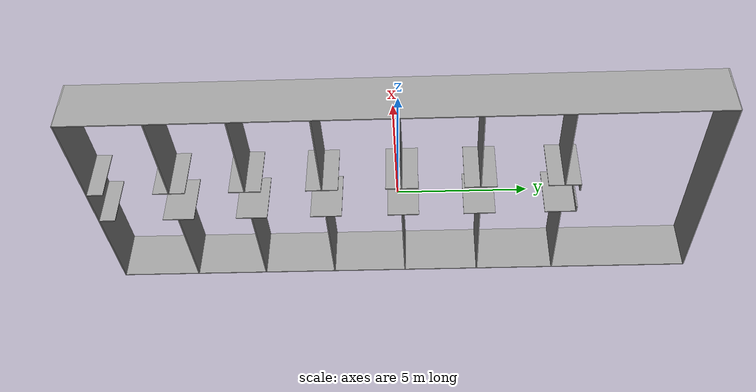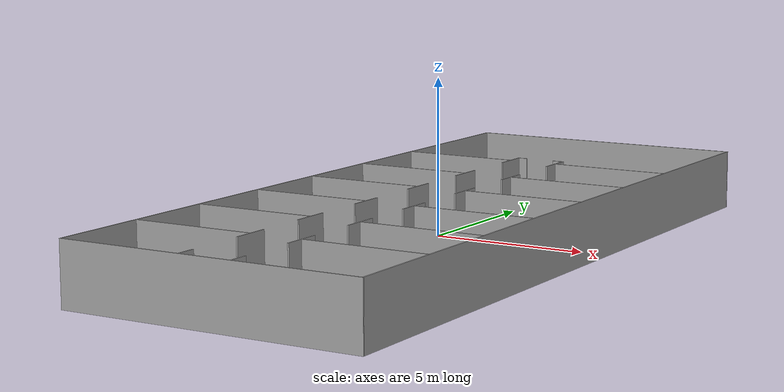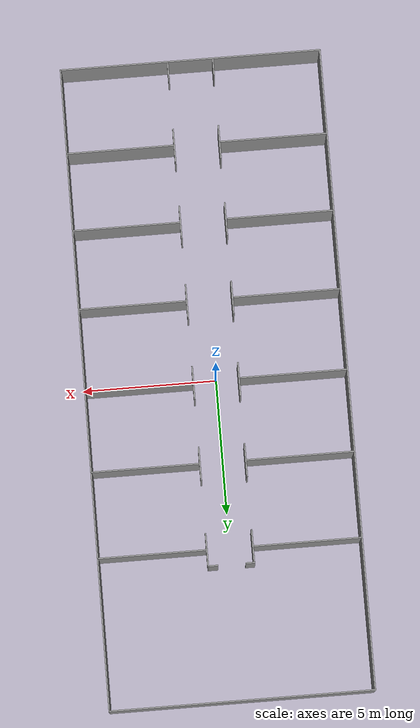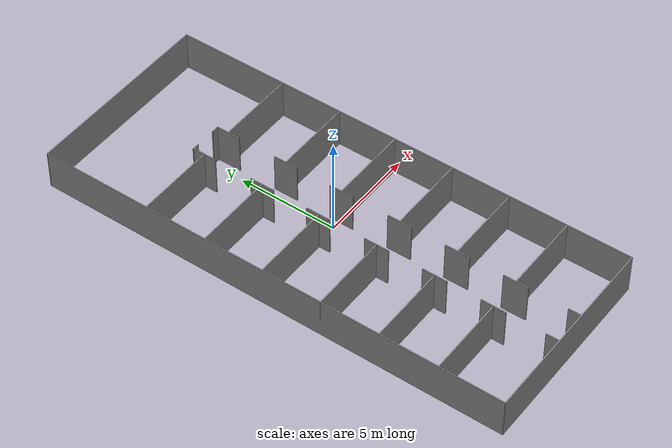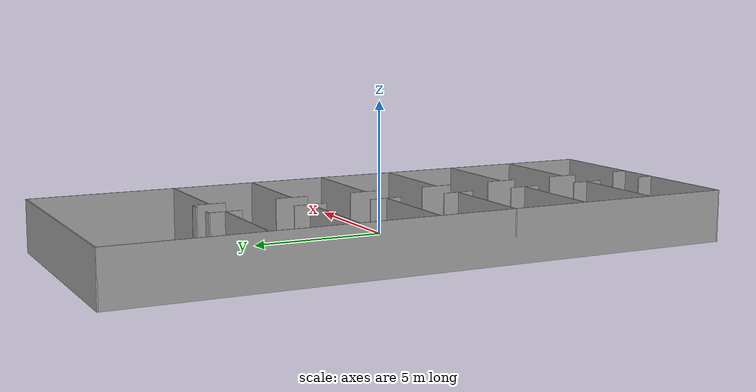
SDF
<?xml version='1.0'?>
<sdf version='1.6'>
  <model name='Straight_corridor_v2'>
    <link name='long_wall_1'>
      <inertial>
        <mass>61760</mass>
        <inertia>
          <ixx>5.2702e+06</ixx>
          <ixy>0</ixy>
          <ixz>0</ixz>
          <iyy>20599.5</iyy>
          <iyz>0</iyz>
          <izz>5.29077e+06</izz>
        </inertia>
        <pose frame=''>0 0 0 0 -0 0</pose>
      </inertial>
      <pose frame=''>-4.875 0 0.5 0 1.57066 0</pose>
      <self_collide>0</self_collide>
      <enable_wind>0</enable_wind>
      <kinematic>0</kinematic>
      <gravity>1</gravity>
      <visual name='visual'>
        <pose frame=''>0 0 0 0 -0 0</pose>
        <geometry>
          <box>
            <size>2 24 0.05</size>
          </box>
        </geometry>
        <material>
          <lighting>1</lighting>
          <script>
            <uri>file://media/materials/scripts/gazebo.material</uri>
            <name>Gazebo/Grey</name>
          </script>
          <shader type='vertex'>
            <normal_map>__default__</normal_map>
          </shader>
          <ambient>0.3 0.3 0.3 1</ambient>
          <diffuse>0.7 0.7 0.7 1</diffuse>
          <specular>0.01 0.01 0.01 1</specular>
          <emissive>0 0 0 1</emissive>
        </material>
        <transparency>0</transparency>
        <cast_shadows>1</cast_shadows>
      </visual>
      <collision name='collision'>
        <laser_retro>0</laser_retro>
        <max_contacts>10</max_contacts>
        <pose frame=''>0 0 0 0 -0 0</pose>
        <geometry>
          <box>
            <size>2 24 0.05</size>
          </box>
        </geometry>
        <surface>
          <friction>
            <ode>
              <mu>1</mu>
              <mu2>1</mu2>
              <fdir1>0 0 0</fdir1>
              <slip1>0</slip1>
              <slip2>0</slip2>
            </ode>
            <torsional>
              <coefficient>1</coefficient>
              <patch_radius>0</patch_radius>
              <surface_radius>0</surface_radius>
              <use_patch_radius>1</use_patch_radius>
              <ode>
                <slip>0</slip>
              </ode>
            </torsional>
          </friction>
          <bounce>
            <restitution_coefficient>0</restitution_coefficient>
            <threshold>1e+06</threshold>
          </bounce>
          <contact>
            <collide_without_contact>0</collide_without_contact>
            <collide_without_contact_bitmask>1</collide_without_contact_bitmask>
            <collide_bitmask>1</collide_bitmask>
            <ode>
              <soft_cfm>0</soft_cfm>
              <soft_erp>0.2</soft_erp>
              <kp>1e+13</kp>
              <kd>1</kd>
              <max_vel>0.01</max_vel>
              <min_depth>0</min_depth>
            </ode>
            <bullet>
              <split_impulse>1</split_impulse>
              <split_impulse_penetration_threshold>-0.01</split_impulse_penetration_threshold>
              <soft_cfm>0</soft_cfm>
              <soft_erp>0.2</soft_erp>
              <kp>1e+13</kp>
              <kd>1</kd>
            </bullet>
          </contact>
        </surface>
      </collision>
    </link>
    <link name='link_0_clone_0'>
      <inertial>
        <mass>30880</mass>
        <inertia>
          <ixx>658780</ixx>
          <ixy>0</ixy>
          <ixz>0</ixz>
          <iyy>10299.8</iyy>
          <iyz>0</iyz>
          <izz>669067</izz>
        </inertia>
        <pose frame=''>0 0 0 0 -0 0</pose>
      </inertial>
      <pose frame=''>-0 -12 0.5 1.58015 1.57079 -3.13224</pose>
      <self_collide>0</self_collide>
      <enable_wind>0</enable_wind>
      <kinematic>0</kinematic>
      <gravity>1</gravity>
      <visual name='visual'>
        <pose frame=''>0 0 0 0 -0 0</pose>
        <geometry>
          <box>
            <size>2 9.8 0.05</size>
          </box>
        </geometry>
        <material>
          <lighting>1</lighting>
          <script>
            <uri>file://media/materials/scripts/gazebo.material</uri>
            <name>Gazebo/Grey</name>
          </script>
          <shader type='pixel'>
            <normal_map>__default__</normal_map>
          </shader>
          <ambient>0.3 0.3 0.3 1</ambient>
          <diffuse>0.7 0.7 0.7 1</diffuse>
          <specular>0.01 0.01 0.01 1</specular>
          <emissive>0 0 0 1</emissive>
        </material>
        <transparency>0</transparency>
        <cast_shadows>1</cast_shadows>
      </visual>
      <collision name='collision'>
        <laser_retro>0</laser_retro>
        <max_contacts>10</max_contacts>
        <pose frame=''>0 0 0 0 -0 0</pose>
        <geometry>
          <box>
            <size>2 9.8 0.05</size>
          </box>
        </geometry>
        <surface>
          <friction>
            <ode>
              <mu>1</mu>
              <mu2>1</mu2>
              <fdir1>0 0 0</fdir1>
              <slip1>0</slip1>
              <slip2>0</slip2>
            </ode>
            <torsional>
              <coefficient>1</coefficient>
              <patch_radius>0</patch_radius>
              <surface_radius>0</surface_radius>
              <use_patch_radius>1</use_patch_radius>
              <ode>
                <slip>0</slip>
              </ode>
            </torsional>
          </friction>
          <bounce>
            <restitution_coefficient>0</restitution_coefficient>
            <threshold>1e+06</threshold>
          </bounce>
          <contact>
            <collide_without_contact>0</collide_without_contact>
            <collide_without_contact_bitmask>1</collide_without_contact_bitmask>
            <collide_bitmask>1</collide_bitmask>
            <ode>
              <soft_cfm>0</soft_cfm>
              <soft_erp>0.2</soft_erp>
              <kp>1e+13</kp>
              <kd>1</kd>
              <max_vel>0.01</max_vel>
              <min_depth>0</min_depth>
            </ode>
            <bullet>
              <split_impulse>1</split_impulse>
              <split_impulse_penetration_threshold>-0.01</split_impulse_penetration_threshold>
              <soft_cfm>0</soft_cfm>
              <soft_erp>0.2</soft_erp>
              <kp>1e+13</kp>
              <kd>1</kd>
            </bullet>
          </contact>
        </surface>
      </collision>
    </link>
    <link name='link_0_clone_1_clone'>
      <inertial>
        <mass>61760</mass>
        <inertia>
          <ixx>5.2702e+06</ixx>
          <ixy>0</ixy>
          <ixz>0</ixz>
          <iyy>20599.5</iyy>
          <iyz>0</iyz>
          <izz>5.29077e+06</izz>
        </inertia>
        <pose frame=''>0 0 0 0 -0 0</pose>
      </inertial>
      <pose frame=''>4.875 -0 0.5 0 1.57051 0</pose>
      <self_collide>0</self_collide>
      <enable_wind>0</enable_wind>
      <kinematic>0</kinematic>
      <gravity>1</gravity>
      <visual name='visual'>
        <pose frame=''>0 0 0 0 -0 0</pose>
        <geometry>
          <box>
            <size>2 24 0.05</size>
          </box>
        </geometry>
        <material>
          <lighting>1</lighting>
          <script>
            <uri>file://media/materials/scripts/gazebo.material</uri>
            <name>Gazebo/Grey</name>
          </script>
          <shader type='vertex'>
            <normal_map>__default__</normal_map>
          </shader>
          <ambient>0.3 0.3 0.3 1</ambient>
          <diffuse>0.7 0.7 0.7 1</diffuse>
          <specular>0.01 0.01 0.01 1</specular>
          <emissive>0 0 0 1</emissive>
        </material>
        <transparency>0</transparency>
        <cast_shadows>1</cast_shadows>
      </visual>
      <collision name='collision'>
        <laser_retro>0</laser_retro>
        <max_contacts>10</max_contacts>
        <pose frame=''>0 0 0 0 -0 0</pose>
        <geometry>
          <box>
            <size>2 24 0.05</size>
          </box>
        </geometry>
        <surface>
          <friction>
            <ode>
              <mu>1</mu>
              <mu2>1</mu2>
              <fdir1>0 0 0</fdir1>
              <slip1>0</slip1>
              <slip2>0</slip2>
            </ode>
            <torsional>
              <coefficient>1</coefficient>
              <patch_radius>0</patch_radius>
              <surface_radius>0</surface_radius>
              <use_patch_radius>1</use_patch_radius>
              <ode>
                <slip>0</slip>
              </ode>
            </torsional>
          </friction>
          <bounce>
            <restitution_coefficient>0</restitution_coefficient>
            <threshold>1e+06</threshold>
          </bounce>
          <contact>
            <collide_without_contact>0</collide_without_contact>
            <collide_without_contact_bitmask>1</collide_without_contact_bitmask>
            <collide_bitmask>1</collide_bitmask>
            <ode>
              <soft_cfm>0</soft_cfm>
              <soft_erp>0.2</soft_erp>
              <kp>1e+13</kp>
              <kd>1</kd>
              <max_vel>0.01</max_vel>
              <min_depth>0</min_depth>
            </ode>
            <bullet>
              <split_impulse>1</split_impulse>
              <split_impulse_penetration_threshold>-0.01</split_impulse_penetration_threshold>
              <soft_cfm>0</soft_cfm>
              <soft_erp>0.2</soft_erp>
              <kp>1e+13</kp>
              <kd>1</kd>
            </bullet>
          </contact>
        </surface>
      </collision>
    </link>
    <link name='link_0_clone_clone'>
      <inertial>
        <mass>2412.5</mass>
        <inertia>
          <ixx>314.63</ixx>
          <ixy>0</ixy>
          <ixz>0</ixz>
          <iyy>804.669</iyy>
          <iyz>0</iyz>
          <izz>1118.29</izz>
        </inertia>
        <pose frame=''>0 0 0 0 -0 0</pose>
      </inertial>
      <pose frame=''>0.85 -8.8 0.500001 3.14159 1.57079 3.14159</pose>
      <self_collide>0</self_collide>
      <enable_wind>0</enable_wind>
      <kinematic>0</kinematic>
      <gravity>1</gravity>
      <visual name='visual'>
        <pose frame=''>0 0 0 0 -0 0</pose>
        <geometry>
          <box>
            <size>2 1.25 0.05</size>
          </box>
        </geometry>
        <material>
          <lighting>1</lighting>
          <script>
            <uri>file://media/materials/scripts/gazebo.material</uri>
            <name>Gazebo/Grey</name>
          </script>
          <shader type='pixel'>
            <normal_map>__default__</normal_map>
          </shader>
          <ambient>0.3 0.3 0.3 1</ambient>
          <diffuse>0.7 0.7 0.7 1</diffuse>
          <specular>0.01 0.01 0.01 1</specular>
          <emissive>0 0 0 1</emissive>
        </material>
        <transparency>0</transparency>
        <cast_shadows>1</cast_shadows>
      </visual>
      <collision name='collision'>
        <laser_retro>0</laser_retro>
        <max_contacts>10</max_contacts>
        <pose frame=''>0 0 0 0 -0 0</pose>
        <geometry>
          <box>
            <size>2 1.25 0.05</size>
          </box>
        </geometry>
        <surface>
          <friction>
            <ode>
              <mu>1</mu>
              <mu2>1</mu2>
              <fdir1>0 0 0</fdir1>
              <slip1>0</slip1>
              <slip2>0</slip2>
            </ode>
            <torsional>
              <coefficient>1</coefficient>
              <patch_radius>0</patch_radius>
              <surface_radius>0</surface_radius>
              <use_patch_radius>1</use_patch_radius>
              <ode>
                <slip>0</slip>
              </ode>
            </torsional>
          </friction>
          <bounce>
            <restitution_coefficient>0</restitution_coefficient>
            <threshold>1e+06</threshold>
          </bounce>
          <contact>
            <collide_without_contact>0</collide_without_contact>
            <collide_without_contact_bitmask>1</collide_without_contact_bitmask>
            <collide_bitmask>1</collide_bitmask>
            <ode>
              <soft_cfm>0</soft_cfm>
              <soft_erp>0.2</soft_erp>
              <kp>1e+13</kp>
              <kd>1</kd>
              <max_vel>0.01</max_vel>
              <min_depth>0</min_depth>
            </ode>
            <bullet>
              <split_impulse>1</split_impulse>
              <split_impulse_penetration_threshold>-0.01</split_impulse_penetration_threshold>
              <soft_cfm>0</soft_cfm>
              <soft_erp>0.2</soft_erp>
              <kp>1e+13</kp>
              <kd>1</kd>
            </bullet>
          </contact>
        </surface>
      </collision>
    </link>
    <link name='link_0_clone_clone_clone'>
      <inertial>
        <mass>2412.5</mass>
        <inertia>
          <ixx>314.63</ixx>
          <ixy>0</ixy>
          <ixz>0</ixz>
          <iyy>804.669</iyy>
          <iyz>0</iyz>
          <izz>1118.29</izz>
        </inertia>
        <pose frame=''>0 0 0 0 -0 0</pose>
      </inertial>
      <pose frame=''>0.85 -5.8665 0.5 0 1.57066 0</pose>
      <self_collide>0</self_collide>
      <enable_wind>0</enable_wind>
      <kinematic>0</kinematic>
      <gravity>1</gravity>
      <visual name='visual'>
        <pose frame=''>0 0 0 0 -0 0</pose>
        <geometry>
          <box>
            <size>2 1.25 0.05</size>
          </box>
        </geometry>
        <material>
          <lighting>1</lighting>
          <script>
            <uri>file://media/materials/scripts/gazebo.material</uri>
            <name>Gazebo/Grey</name>
          </script>
          <shader type='pixel'>
            <normal_map>__default__</normal_map>
          </shader>
          <ambient>0.3 0.3 0.3 1</ambient>
          <diffuse>0.7 0.7 0.7 1</diffuse>
          <specular>0.01 0.01 0.01 1</specular>
          <emissive>0 0 0 1</emissive>
        </material>
        <transparency>0</transparency>
        <cast_shadows>1</cast_shadows>
      </visual>
      <collision name='collision'>
        <laser_retro>0</laser_retro>
        <max_contacts>10</max_contacts>
        <pose frame=''>0 0 0 0 -0 0</pose>
        <geometry>
          <box>
            <size>2 1.25 0.05</size>
          </box>
        </geometry>
        <surface>
          <friction>
            <ode>
              <mu>1</mu>
              <mu2>1</mu2>
              <fdir1>0 0 0</fdir1>
              <slip1>0</slip1>
              <slip2>0</slip2>
            </ode>
            <torsional>
              <coefficient>1</coefficient>
              <patch_radius>0</patch_radius>
              <surface_radius>0</surface_radius>
              <use_patch_radius>1</use_patch_radius>
              <ode>
                <slip>0</slip>
              </ode>
            </torsional>
          </friction>
          <bounce>
            <restitution_coefficient>0</restitution_coefficient>
            <threshold>1e+06</threshold>
          </bounce>
          <contact>
            <collide_without_contact>0</collide_without_contact>
            <collide_without_contact_bitmask>1</collide_without_contact_bitmask>
            <collide_bitmask>1</collide_bitmask>
            <ode>
              <soft_cfm>0</soft_cfm>
              <soft_erp>0.2</soft_erp>
              <kp>1e+13</kp>
              <kd>1</kd>
              <max_vel>0.01</max_vel>
              <min_depth>0</min_depth>
            </ode>
            <bullet>
              <split_impulse>1</split_impulse>
              <split_impulse_penetration_threshold>-0.01</split_impulse_penetration_threshold>
              <soft_cfm>0</soft_cfm>
              <soft_erp>0.2</soft_erp>
              <kp>1e+13</kp>
              <kd>1</kd>
            </bullet>
          </contact>
        </surface>
      </collision>
    </link>
    <link name='link_0_clone_clone_clone_0'>
      <inertial>
        <mass>2412.5</mass>
        <inertia>
          <ixx>314.63</ixx>
          <ixy>0</ixy>
          <ixz>0</ixz>
          <iyy>804.669</iyy>
          <iyz>0</iyz>
          <izz>1118.29</izz>
        </inertia>
        <pose frame=''>0 0 0 0 -0 0</pose>
      </inertial>
      <pose frame=''>0.85 -2.895 0.5 0 1.57066 0</pose>
      <self_collide>0</self_collide>
      <enable_wind>0</enable_wind>
      <kinematic>0</kinematic>
      <gravity>1</gravity>
      <visual name='visual'>
        <pose frame=''>0 0 0 0 -0 0</pose>
        <geometry>
          <box>
            <size>2 1.25 0.05</size>
          </box>
        </geometry>
        <material>
          <lighting>1</lighting>
          <script>
            <uri>file://media/materials/scripts/gazebo.material</uri>
            <name>Gazebo/Grey</name>
          </script>
          <shader type='pixel'>
            <normal_map>__default__</normal_map>
          </shader>
          <ambient>0.3 0.3 0.3 1</ambient>
          <diffuse>0.7 0.7 0.7 1</diffuse>
          <specular>0.01 0.01 0.01 1</specular>
          <emissive>0 0 0 1</emissive>
        </material>
        <transparency>0</transparency>
        <cast_shadows>1</cast_shadows>
      </visual>
      <collision name='collision'>
        <laser_retro>0</laser_retro>
        <max_contacts>10</max_contacts>
        <pose frame=''>0 0 0 0 -0 0</pose>
        <geometry>
          <box>
            <size>2 1.25 0.05</size>
          </box>
        </geometry>
        <surface>
          <friction>
            <ode>
              <mu>1</mu>
              <mu2>1</mu2>
              <fdir1>0 0 0</fdir1>
              <slip1>0</slip1>
              <slip2>0</slip2>
            </ode>
            <torsional>
              <coefficient>1</coefficient>
              <patch_radius>0</patch_radius>
              <surface_radius>0</surface_radius>
              <use_patch_radius>1</use_patch_radius>
              <ode>
                <slip>0</slip>
              </ode>
            </torsional>
          </friction>
          <bounce>
            <restitution_coefficient>0</restitution_coefficient>
            <threshold>1e+06</threshold>
          </bounce>
          <contact>
            <collide_without_contact>0</collide_without_contact>
            <collide_without_contact_bitmask>1</collide_without_contact_bitmask>
            <collide_bitmask>1</collide_bitmask>
            <ode>
              <soft_cfm>0</soft_cfm>
              <soft_erp>0.2</soft_erp>
              <kp>1e+13</kp>
              <kd>1</kd>
              <max_vel>0.01</max_vel>
              <min_depth>0</min_depth>
            </ode>
            <bullet>
              <split_impulse>1</split_impulse>
              <split_impulse_penetration_threshold>-0.01</split_impulse_penetration_threshold>
              <soft_cfm>0</soft_cfm>
              <soft_erp>0.2</soft_erp>
              <kp>1e+13</kp>
              <kd>1</kd>
            </bullet>
          </contact>
        </surface>
      </collision>
    </link>
    <link name='link_0_clone_clone_clone_0_clone'>
      <inertial>
        <mass>2412.5</mass>
        <inertia>
          <ixx>314.63</ixx>
          <ixy>0</ixy>
          <ixz>0</ixz>
          <iyy>804.669</iyy>
          <iyz>0</iyz>
          <izz>1118.29</izz>
        </inertia>
        <pose frame=''>0 0 0 0 -0 0</pose>
      </inertial>
      <pose frame=''>-0.85 -2.895 0.5 0 1.57051 0</pose>
      <self_collide>0</self_collide>
      <enable_wind>0</enable_wind>
      <kinematic>0</kinematic>
      <gravity>1</gravity>
      <visual name='visual'>
        <pose frame=''>0 0 0 0 -0 0</pose>
        <geometry>
          <box>
            <size>2 1.25 0.05</size>
          </box>
        </geometry>
        <material>
          <lighting>1</lighting>
          <script>
            <uri>file://media/materials/scripts/gazebo.material</uri>
            <name>Gazebo/Grey</name>
          </script>
          <shader type='pixel'>
            <normal_map>__default__</normal_map>
          </shader>
          <ambient>0.3 0.3 0.3 1</ambient>
          <diffuse>0.7 0.7 0.7 1</diffuse>
          <specular>0.01 0.01 0.01 1</specular>
          <emissive>0 0 0 1</emissive>
        </material>
        <transparency>0</transparency>
        <cast_shadows>1</cast_shadows>
      </visual>
      <collision name='collision'>
        <laser_retro>0</laser_retro>
        <max_contacts>10</max_contacts>
        <pose frame=''>0 0 0 0 -0 0</pose>
        <geometry>
          <box>
            <size>2 1.25 0.05</size>
          </box>
        </geometry>
        <surface>
          <friction>
            <ode>
              <mu>1</mu>
              <mu2>1</mu2>
              <fdir1>0 0 0</fdir1>
              <slip1>0</slip1>
              <slip2>0</slip2>
            </ode>
            <torsional>
              <coefficient>1</coefficient>
              <patch_radius>0</patch_radius>
              <surface_radius>0</surface_radius>
              <use_patch_radius>1</use_patch_radius>
              <ode>
                <slip>0</slip>
              </ode>
            </torsional>
          </friction>
          <bounce>
            <restitution_coefficient>0</restitution_coefficient>
            <threshold>1e+06</threshold>
          </bounce>
          <contact>
            <collide_without_contact>0</collide_without_contact>
            <collide_without_contact_bitmask>1</collide_without_contact_bitmask>
            <collide_bitmask>1</collide_bitmask>
            <ode>
              <soft_cfm>0</soft_cfm>
              <soft_erp>0.2</soft_erp>
              <kp>1e+13</kp>
              <kd>1</kd>
              <max_vel>0.01</max_vel>
              <min_depth>0</min_depth>
            </ode>
            <bullet>
              <split_impulse>1</split_impulse>
              <split_impulse_penetration_threshold>-0.01</split_impulse_penetration_threshold>
              <soft_cfm>0</soft_cfm>
              <soft_erp>0.2</soft_erp>
              <kp>1e+13</kp>
              <kd>1</kd>
            </bullet>
          </contact>
        </surface>
      </collision>
    </link>
    <link name='link_0_clone_clone_clone_1'>
      <inertial>
        <mass>2412.5</mass>
        <inertia>
          <ixx>314.63</ixx>
          <ixy>0</ixy>
          <ixz>0</ixz>
          <iyy>804.669</iyy>
          <iyz>0</iyz>
          <izz>1118.29</izz>
        </inertia>
        <pose frame=''>0 0 0 0 -0 0</pose>
      </inertial>
      <pose frame=''>0.85 0.1777 0.5 0 1.57066 0</pose>
      <self_collide>0</self_collide>
      <enable_wind>0</enable_wind>
      <kinematic>0</kinematic>
      <gravity>1</gravity>
      <visual name='visual'>
        <pose frame=''>0 0 0 0 -0 0</pose>
        <geometry>
          <box>
            <size>2 1.25 0.05</size>
          </box>
        </geometry>
        <material>
          <lighting>1</lighting>
          <script>
            <uri>file://media/materials/scripts/gazebo.material</uri>
            <name>Gazebo/Grey</name>
          </script>
          <shader type='pixel'>
            <normal_map>__default__</normal_map>
          </shader>
          <ambient>0.3 0.3 0.3 1</ambient>
          <diffuse>0.7 0.7 0.7 1</diffuse>
          <specular>0.01 0.01 0.01 1</specular>
          <emissive>0 0 0 1</emissive>
        </material>
        <transparency>0</transparency>
        <cast_shadows>1</cast_shadows>
      </visual>
      <collision name='collision'>
        <laser_retro>0</laser_retro>
        <max_contacts>10</max_contacts>
        <pose frame=''>0 0 0 0 -0 0</pose>
        <geometry>
          <box>
            <size>2 1.25 0.05</size>
          </box>
        </geometry>
        <surface>
          <friction>
            <ode>
              <mu>1</mu>
              <mu2>1</mu2>
              <fdir1>0 0 0</fdir1>
              <slip1>0</slip1>
              <slip2>0</slip2>
            </ode>
            <torsional>
              <coefficient>1</coefficient>
              <patch_radius>0</patch_radius>
              <surface_radius>0</surface_radius>
              <use_patch_radius>1</use_patch_radius>
              <ode>
                <slip>0</slip>
              </ode>
            </torsional>
          </friction>
          <bounce>
            <restitution_coefficient>0</restitution_coefficient>
            <threshold>1e+06</threshold>
          </bounce>
          <contact>
            <collide_without_contact>0</collide_without_contact>
            <collide_without_contact_bitmask>1</collide_without_contact_bitmask>
            <collide_bitmask>1</collide_bitmask>
            <ode>
              <soft_cfm>0</soft_cfm>
              <soft_erp>0.2</soft_erp>
              <kp>1e+13</kp>
              <kd>1</kd>
              <max_vel>0.01</max_vel>
              <min_depth>0</min_depth>
            </ode>
            <bullet>
              <split_impulse>1</split_impulse>
              <split_impulse_penetration_threshold>-0.01</split_impulse_penetration_threshold>
              <soft_cfm>0</soft_cfm>
              <soft_erp>0.2</soft_erp>
              <kp>1e+13</kp>
              <kd>1</kd>
            </bullet>
          </contact>
        </surface>
      </collision>
    </link>
    <link name='link_0_clone_clone_clone_1_clone'>
      <inertial>
        <mass>2412.5</mass>
        <inertia>
          <ixx>314.63</ixx>
          <ixy>0</ixy>
          <ixz>0</ixz>
          <iyy>804.669</iyy>
          <iyz>0</iyz>
          <izz>1118.29</izz>
        </inertia>
        <pose frame=''>0 0 0 0 -0 0</pose>
      </inertial>
      <pose frame=''>-0.85 0.17777 0.5 0 1.57051 0</pose>
      <self_collide>0</self_collide>
      <enable_wind>0</enable_wind>
      <kinematic>0</kinematic>
      <gravity>1</gravity>
      <visual name='visual'>
        <pose frame=''>0 0 0 0 -0 0</pose>
        <geometry>
          <box>
            <size>2 1.25 0.05</size>
          </box>
        </geometry>
        <material>
          <lighting>1</lighting>
          <script>
            <uri>file://media/materials/scripts/gazebo.material</uri>
            <name>Gazebo/Grey</name>
          </script>
          <shader type='pixel'>
            <normal_map>__default__</normal_map>
          </shader>
          <ambient>0.3 0.3 0.3 1</ambient>
          <diffuse>0.7 0.7 0.7 1</diffuse>
          <specular>0.01 0.01 0.01 1</specular>
          <emissive>0 0 0 1</emissive>
        </material>
        <transparency>0</transparency>
        <cast_shadows>1</cast_shadows>
      </visual>
      <collision name='collision'>
        <laser_retro>0</laser_retro>
        <max_contacts>10</max_contacts>
        <pose frame=''>0 0 0 0 -0 0</pose>
        <geometry>
          <box>
            <size>2 1.25 0.05</size>
          </box>
        </geometry>
        <surface>
          <friction>
            <ode>
              <mu>1</mu>
              <mu2>1</mu2>
              <fdir1>0 0 0</fdir1>
              <slip1>0</slip1>
              <slip2>0</slip2>
            </ode>
            <torsional>
              <coefficient>1</coefficient>
              <patch_radius>0</patch_radius>
              <surface_radius>0</surface_radius>
              <use_patch_radius>1</use_patch_radius>
              <ode>
                <slip>0</slip>
              </ode>
            </torsional>
          </friction>
          <bounce>
            <restitution_coefficient>0</restitution_coefficient>
            <threshold>1e+06</threshold>
          </bounce>
          <contact>
            <collide_without_contact>0</collide_without_contact>
            <collide_without_contact_bitmask>1</collide_without_contact_bitmask>
            <collide_bitmask>1</collide_bitmask>
            <ode>
              <soft_cfm>0</soft_cfm>
              <soft_erp>0.2</soft_erp>
              <kp>1e+13</kp>
              <kd>1</kd>
              <max_vel>0.01</max_vel>
              <min_depth>0</min_depth>
            </ode>
            <bullet>
              <split_impulse>1</split_impulse>
              <split_impulse_penetration_threshold>-0.01</split_impulse_penetration_threshold>
              <soft_cfm>0</soft_cfm>
              <soft_erp>0.2</soft_erp>
              <kp>1e+13</kp>
              <kd>1</kd>
            </bullet>
          </contact>
        </surface>
      </collision>
    </link>
    <link name='link_0_clone_clone_clone_2'>
      <inertial>
        <mass>2412.5</mass>
        <inertia>
          <ixx>314.63</ixx>
          <ixy>0</ixy>
          <ixz>0</ixz>
          <iyy>804.669</iyy>
          <iyz>0</iyz>
          <izz>1118.29</izz>
        </inertia>
        <pose frame=''>0 0 0 0 -0 0</pose>
      </inertial>
      <pose frame=''>0.85 3.2 0.5 0 1.57066 0</pose>
      <self_collide>0</self_collide>
      <enable_wind>0</enable_wind>
      <kinematic>0</kinematic>
      <gravity>1</gravity>
      <visual name='visual'>
        <pose frame=''>0 0 0 0 -0 0</pose>
        <geometry>
          <box>
            <size>2 1.25 0.05</size>
          </box>
        </geometry>
        <material>
          <lighting>1</lighting>
          <script>
            <uri>file://media/materials/scripts/gazebo.material</uri>
            <name>Gazebo/Grey</name>
          </script>
          <shader type='pixel'>
            <normal_map>__default__</normal_map>
          </shader>
          <ambient>0.3 0.3 0.3 1</ambient>
          <diffuse>0.7 0.7 0.7 1</diffuse>
          <specular>0.01 0.01 0.01 1</specular>
          <emissive>0 0 0 1</emissive>
        </material>
        <transparency>0</transparency>
        <cast_shadows>1</cast_shadows>
      </visual>
      <collision name='collision'>
        <laser_retro>0</laser_retro>
        <max_contacts>10</max_contacts>
        <pose frame=''>0 0 0 0 -0 0</pose>
        <geometry>
          <box>
            <size>2 1.25 0.05</size>
          </box>
        </geometry>
        <surface>
          <friction>
            <ode>
              <mu>1</mu>
              <mu2>1</mu2>
              <fdir1>0 0 0</fdir1>
              <slip1>0</slip1>
              <slip2>0</slip2>
            </ode>
            <torsional>
              <coefficient>1</coefficient>
              <patch_radius>0</patch_radius>
              <surface_radius>0</surface_radius>
              <use_patch_radius>1</use_patch_radius>
              <ode>
                <slip>0</slip>
              </ode>
            </torsional>
          </friction>
          <bounce>
            <restitution_coefficient>0</restitution_coefficient>
            <threshold>1e+06</threshold>
          </bounce>
          <contact>
            <collide_without_contact>0</collide_without_contact>
            <collide_without_contact_bitmask>1</collide_without_contact_bitmask>
            <collide_bitmask>1</collide_bitmask>
            <ode>
              <soft_cfm>0</soft_cfm>
              <soft_erp>0.2</soft_erp>
              <kp>1e+13</kp>
              <kd>1</kd>
              <max_vel>0.01</max_vel>
              <min_depth>0</min_depth>
            </ode>
            <bullet>
              <split_impulse>1</split_impulse>
              <split_impulse_penetration_threshold>-0.01</split_impulse_penetration_threshold>
              <soft_cfm>0</soft_cfm>
              <soft_erp>0.2</soft_erp>
              <kp>1e+13</kp>
              <kd>1</kd>
            </bullet>
          </contact>
        </surface>
      </collision>
    </link>
    <link name='link_0_clone_clone_clone_2_clone'>
      <inertial>
        <mass>2412.5</mass>
        <inertia>
          <ixx>314.63</ixx>
          <ixy>0</ixy>
          <ixz>0</ixz>
          <iyy>804.669</iyy>
          <iyz>0</iyz>
          <izz>1118.29</izz>
        </inertia>
        <pose frame=''>0 0 0 0 -0 0</pose>
      </inertial>
      <pose frame=''>-0.85 3.2 0.5 0 1.57051 0</pose>
      <self_collide>0</self_collide>
      <enable_wind>0</enable_wind>
      <kinematic>0</kinematic>
      <gravity>1</gravity>
      <visual name='visual'>
        <pose frame=''>0 0 0 0 -0 0</pose>
        <geometry>
          <box>
            <size>2 1.25 0.05</size>
          </box>
        </geometry>
        <material>
          <lighting>1</lighting>
          <script>
            <uri>file://media/materials/scripts/gazebo.material</uri>
            <name>Gazebo/Grey</name>
          </script>
          <shader type='pixel'>
            <normal_map>__default__</normal_map>
          </shader>
          <ambient>0.3 0.3 0.3 1</ambient>
          <diffuse>0.7 0.7 0.7 1</diffuse>
          <specular>0.01 0.01 0.01 1</specular>
          <emissive>0 0 0 1</emissive>
        </material>
        <transparency>0</transparency>
        <cast_shadows>1</cast_shadows>
      </visual>
      <collision name='collision'>
        <laser_retro>0</laser_retro>
        <max_contacts>10</max_contacts>
        <pose frame=''>0 0 0 0 -0 0</pose>
        <geometry>
          <box>
            <size>2 1.25 0.05</size>
          </box>
        </geometry>
        <surface>
          <friction>
            <ode>
              <mu>1</mu>
              <mu2>1</mu2>
              <fdir1>0 0 0</fdir1>
              <slip1>0</slip1>
              <slip2>0</slip2>
            </ode>
            <torsional>
              <coefficient>1</coefficient>
              <patch_radius>0</patch_radius>
              <surface_radius>0</surface_radius>
              <use_patch_radius>1</use_patch_radius>
              <ode>
                <slip>0</slip>
              </ode>
            </torsional>
          </friction>
          <bounce>
            <restitution_coefficient>0</restitution_coefficient>
            <threshold>1e+06</threshold>
          </bounce>
          <contact>
            <collide_without_contact>0</collide_without_contact>
            <collide_without_contact_bitmask>1</collide_without_contact_bitmask>
            <collide_bitmask>1</collide_bitmask>
            <ode>
              <soft_cfm>0</soft_cfm>
              <soft_erp>0.2</soft_erp>
              <kp>1e+13</kp>
              <kd>1</kd>
              <max_vel>0.01</max_vel>
              <min_depth>0</min_depth>
            </ode>
            <bullet>
              <split_impulse>1</split_impulse>
              <split_impulse_penetration_threshold>-0.01</split_impulse_penetration_threshold>
              <soft_cfm>0</soft_cfm>
              <soft_erp>0.2</soft_erp>
              <kp>1e+13</kp>
              <kd>1</kd>
            </bullet>
          </contact>
        </surface>
      </collision>
    </link>
    <link name='link_0_clone_clone_clone_3'>
      <inertial>
        <mass>2412.5</mass>
        <inertia>
          <ixx>314.63</ixx>
          <ixy>0</ixy>
          <ixz>0</ixz>
          <iyy>804.669</iyy>
          <iyz>0</iyz>
          <izz>1118.29</izz>
        </inertia>
        <pose frame=''>0 0 0 0 -0 0</pose>
      </inertial>
      <pose frame=''>0.85 6.3975 0.5 0 1.57066 0</pose>
      <self_collide>0</self_collide>
      <enable_wind>0</enable_wind>
      <kinematic>0</kinematic>
      <gravity>1</gravity>
      <visual name='visual'>
        <pose frame=''>0 0 0 0 -0 0</pose>
        <geometry>
          <box>
            <size>2 1.25 0.05</size>
          </box>
        </geometry>
        <material>
          <lighting>1</lighting>
          <script>
            <uri>file://media/materials/scripts/gazebo.material</uri>
            <name>Gazebo/Grey</name>
          </script>
          <shader type='pixel'>
            <normal_map>__default__</normal_map>
          </shader>
          <ambient>0.3 0.3 0.3 1</ambient>
          <diffuse>0.7 0.7 0.7 1</diffuse>
          <specular>0.01 0.01 0.01 1</specular>
          <emissive>0 0 0 1</emissive>
        </material>
        <transparency>0</transparency>
        <cast_shadows>1</cast_shadows>
      </visual>
      <collision name='collision'>
        <laser_retro>0</laser_retro>
        <max_contacts>10</max_contacts>
        <pose frame=''>0 0 0 0 -0 0</pose>
        <geometry>
          <box>
            <size>2 1.25 0.05</size>
          </box>
        </geometry>
        <surface>
          <friction>
            <ode>
              <mu>1</mu>
              <mu2>1</mu2>
              <fdir1>0 0 0</fdir1>
              <slip1>0</slip1>
              <slip2>0</slip2>
            </ode>
            <torsional>
              <coefficient>1</coefficient>
              <patch_radius>0</patch_radius>
              <surface_radius>0</surface_radius>
              <use_patch_radius>1</use_patch_radius>
              <ode>
                <slip>0</slip>
              </ode>
            </torsional>
          </friction>
          <bounce>
            <restitution_coefficient>0</restitution_coefficient>
            <threshold>1e+06</threshold>
          </bounce>
          <contact>
            <collide_without_contact>0</collide_without_contact>
            <collide_without_contact_bitmask>1</collide_without_contact_bitmask>
            <collide_bitmask>1</collide_bitmask>
            <ode>
              <soft_cfm>0</soft_cfm>
              <soft_erp>0.2</soft_erp>
              <kp>1e+13</kp>
              <kd>1</kd>
              <max_vel>0.01</max_vel>
              <min_depth>0</min_depth>
            </ode>
            <bullet>
              <split_impulse>1</split_impulse>
              <split_impulse_penetration_threshold>-0.01</split_impulse_penetration_threshold>
              <soft_cfm>0</soft_cfm>
              <soft_erp>0.2</soft_erp>
              <kp>1e+13</kp>
              <kd>1</kd>
            </bullet>
          </contact>
        </surface>
      </collision>
    </link>
    <link name='link_0_clone_clone_clone_3_clone'>
      <inertial>
        <mass>2412.5</mass>
        <inertia>
          <ixx>314.63</ixx>
          <ixy>0</ixy>
          <ixz>0</ixz>
          <iyy>804.669</iyy>
          <iyz>0</iyz>
          <izz>1118.29</izz>
        </inertia>
        <pose frame=''>0 0 0 0 -0 0</pose>
      </inertial>
      <pose frame=''>-0.85 6.3975 0.5 0 1.57051 0</pose>
      <self_collide>0</self_collide>
      <enable_wind>0</enable_wind>
      <kinematic>0</kinematic>
      <gravity>1</gravity>
      <visual name='visual'>
        <pose frame=''>0 0 0 0 -0 0</pose>
        <geometry>
          <box>
            <size>2 1.25 0.05</size>
          </box>
        </geometry>
        <material>
          <lighting>1</lighting>
          <script>
            <uri>file://media/materials/scripts/gazebo.material</uri>
            <name>Gazebo/Grey</name>
          </script>
          <shader type='pixel'>
            <normal_map>__default__</normal_map>
          </shader>
          <ambient>0.3 0.3 0.3 1</ambient>
          <diffuse>0.7 0.7 0.7 1</diffuse>
          <specular>0.01 0.01 0.01 1</specular>
          <emissive>0 0 0 1</emissive>
        </material>
        <transparency>0</transparency>
        <cast_shadows>1</cast_shadows>
      </visual>
      <collision name='collision'>
        <laser_retro>0</laser_retro>
        <max_contacts>10</max_contacts>
        <pose frame=''>0 0 0 0 -0 0</pose>
        <geometry>
          <box>
            <size>2 1.25 0.05</size>
          </box>
        </geometry>
        <surface>
          <friction>
            <ode>
              <mu>1</mu>
              <mu2>1</mu2>
              <fdir1>0 0 0</fdir1>
              <slip1>0</slip1>
              <slip2>0</slip2>
            </ode>
            <torsional>
              <coefficient>1</coefficient>
              <patch_radius>0</patch_radius>
              <surface_radius>0</surface_radius>
              <use_patch_radius>1</use_patch_radius>
              <ode>
                <slip>0</slip>
              </ode>
            </torsional>
          </friction>
          <bounce>
            <restitution_coefficient>0</restitution_coefficient>
            <threshold>1e+06</threshold>
          </bounce>
          <contact>
            <collide_without_contact>0</collide_without_contact>
            <collide_without_contact_bitmask>1</collide_without_contact_bitmask>
            <collide_bitmask>1</collide_bitmask>
            <ode>
              <soft_cfm>0</soft_cfm>
              <soft_erp>0.2</soft_erp>
              <kp>1e+13</kp>
              <kd>1</kd>
              <max_vel>0.01</max_vel>
              <min_depth>0</min_depth>
            </ode>
            <bullet>
              <split_impulse>1</split_impulse>
              <split_impulse_penetration_threshold>-0.01</split_impulse_penetration_threshold>
              <soft_cfm>0</soft_cfm>
              <soft_erp>0.2</soft_erp>
              <kp>1e+13</kp>
              <kd>1</kd>
            </bullet>
          </contact>
        </surface>
      </collision>
    </link>
    <link name='link_0_clone_clone_clone_4'>
      <inertial>
        <mass>1206.25</mass>
        <inertia>
          <ixx>39.5173</ixx>
          <ixy>0</ixy>
          <ixz>0</ixz>
          <iyy>402.335</iyy>
          <iyz>0</iyz>
          <izz>441.349</izz>
        </inertia>
        <pose frame=''>0 0 0 0 -0 0</pose>
      </inertial>
      <pose frame=''>0.85 -11.6736 0.5 0 1.57066 0</pose>
      <self_collide>0</self_collide>
      <enable_wind>0</enable_wind>
      <kinematic>0</kinematic>
      <gravity>1</gravity>
      <visual name='visual'>
        <pose frame=''>0 0 0 0 -0 0</pose>
        <geometry>
          <box>
            <size>2 0.625 0.05</size>
          </box>
        </geometry>
        <material>
          <lighting>1</lighting>
          <script>
            <uri>file://media/materials/scripts/gazebo.material</uri>
            <name>Gazebo/Grey</name>
          </script>
          <shader type='pixel'>
            <normal_map>__default__</normal_map>
          </shader>
          <ambient>0.3 0.3 0.3 1</ambient>
          <diffuse>0.7 0.7 0.7 1</diffuse>
          <specular>0.01 0.01 0.01 1</specular>
          <emissive>0 0 0 1</emissive>
        </material>
        <transparency>0</transparency>
        <cast_shadows>1</cast_shadows>
      </visual>
      <collision name='collision'>
        <laser_retro>0</laser_retro>
        <max_contacts>10</max_contacts>
        <pose frame=''>0 0 0 0 -0 0</pose>
        <geometry>
          <box>
            <size>2 0.625 0.05</size>
          </box>
        </geometry>
        <surface>
          <friction>
            <ode>
              <mu>1</mu>
              <mu2>1</mu2>
              <fdir1>0 0 0</fdir1>
              <slip1>0</slip1>
              <slip2>0</slip2>
            </ode>
            <torsional>
              <coefficient>1</coefficient>
              <patch_radius>0</patch_radius>
              <surface_radius>0</surface_radius>
              <use_patch_radius>1</use_patch_radius>
              <ode>
                <slip>0</slip>
              </ode>
            </torsional>
          </friction>
          <bounce>
            <restitution_coefficient>0</restitution_coefficient>
            <threshold>1e+06</threshold>
          </bounce>
          <contact>
            <collide_without_contact>0</collide_without_contact>
            <collide_without_contact_bitmask>1</collide_without_contact_bitmask>
            <collide_bitmask>1</collide_bitmask>
            <ode>
              <soft_cfm>0</soft_cfm>
              <soft_erp>0.2</soft_erp>
              <kp>1e+13</kp>
              <kd>1</kd>
              <max_vel>0.01</max_vel>
              <min_depth>0</min_depth>
            </ode>
            <bullet>
              <split_impulse>1</split_impulse>
              <split_impulse_penetration_threshold>-0.01</split_impulse_penetration_threshold>
              <soft_cfm>0</soft_cfm>
              <soft_erp>0.2</soft_erp>
              <kp>1e+13</kp>
              <kd>1</kd>
            </bullet>
          </contact>
        </surface>
      </collision>
    </link>
    <link name='link_0_clone_clone_clone_4_clone'>
      <inertial>
        <mass>1206.25</mass>
        <inertia>
          <ixx>39.5173</ixx>
          <ixy>0</ixy>
          <ixz>0</ixz>
          <iyy>402.335</iyy>
          <iyz>0</iyz>
          <izz>441.349</izz>
        </inertia>
        <pose frame=''>0 0 0 0 -0 0</pose>
      </inertial>
      <pose frame=''>-0.85 -11.6649 0.5 0 1.57051 0</pose>
      <self_collide>0</self_collide>
      <enable_wind>0</enable_wind>
      <kinematic>0</kinematic>
      <gravity>1</gravity>
      <visual name='visual'>
        <pose frame=''>0 0 0 0 -0 0</pose>
        <geometry>
          <box>
            <size>2 0.625 0.05</size>
          </box>
        </geometry>
        <material>
          <lighting>1</lighting>
          <script>
            <uri>file://media/materials/scripts/gazebo.material</uri>
            <name>Gazebo/Grey</name>
          </script>
          <shader type='pixel'>
            <normal_map>__default__</normal_map>
          </shader>
          <ambient>0.3 0.3 0.3 1</ambient>
          <diffuse>0.7 0.7 0.7 1</diffuse>
          <specular>0.01 0.01 0.01 1</specular>
          <emissive>0 0 0 1</emissive>
        </material>
        <transparency>0</transparency>
        <cast_shadows>1</cast_shadows>
      </visual>
      <collision name='collision'>
        <laser_retro>0</laser_retro>
        <max_contacts>10</max_contacts>
        <pose frame=''>0 0 0 0 -0 0</pose>
        <geometry>
          <box>
            <size>2 0.625 0.05</size>
          </box>
        </geometry>
        <surface>
          <friction>
            <ode>
              <mu>1</mu>
              <mu2>1</mu2>
              <fdir1>0 0 0</fdir1>
              <slip1>0</slip1>
              <slip2>0</slip2>
            </ode>
            <torsional>
              <coefficient>1</coefficient>
              <patch_radius>0</patch_radius>
              <surface_radius>0</surface_radius>
              <use_patch_radius>1</use_patch_radius>
              <ode>
                <slip>0</slip>
              </ode>
            </torsional>
          </friction>
          <bounce>
            <restitution_coefficient>0</restitution_coefficient>
            <threshold>1e+06</threshold>
          </bounce>
          <contact>
            <collide_without_contact>0</collide_without_contact>
            <collide_without_contact_bitmask>1</collide_without_contact_bitmask>
            <collide_bitmask>1</collide_bitmask>
            <ode>
              <soft_cfm>0</soft_cfm>
              <soft_erp>0.2</soft_erp>
              <kp>1e+13</kp>
              <kd>1</kd>
              <max_vel>0.01</max_vel>
              <min_depth>0</min_depth>
            </ode>
            <bullet>
              <split_impulse>1</split_impulse>
              <split_impulse_penetration_threshold>-0.01</split_impulse_penetration_threshold>
              <soft_cfm>0</soft_cfm>
              <soft_erp>0.2</soft_erp>
              <kp>1e+13</kp>
              <kd>1</kd>
            </bullet>
          </contact>
        </surface>
      </collision>
    </link>
    <link name='link_0_clone_clone_clone_4_clone_0'>
      <inertial>
        <mass>1206.25</mass>
        <inertia>
          <ixx>39.5173</ixx>
          <ixy>0</ixy>
          <ixz>0</ixz>
          <iyy>402.335</iyy>
          <iyz>0</iyz>
          <izz>441.349</izz>
        </inertia>
        <pose frame=''>0 0 0 0 -0 0</pose>
      </inertial>
      <pose frame=''>0.65382 7.00009 0.499911 -1.5708 1.57051 3e-06</pose>
      <self_collide>0</self_collide>
      <enable_wind>0</enable_wind>
      <kinematic>0</kinematic>
      <gravity>1</gravity>
      <visual name='visual'>
        <pose frame=''>0 0 0 0 -0 0</pose>
        <geometry>
          <box>
            <size>2 0.35 0.05</size>
          </box>
        </geometry>
        <material>
          <lighting>1</lighting>
          <script>
            <uri>file://media/materials/scripts/gazebo.material</uri>
            <name>Gazebo/Grey</name>
          </script>
          <shader type='pixel'>
            <normal_map>__default__</normal_map>
          </shader>
          <ambient>0.3 0.3 0.3 1</ambient>
          <diffuse>0.7 0.7 0.7 1</diffuse>
          <specular>0.01 0.01 0.01 1</specular>
          <emissive>0 0 0 1</emissive>
        </material>
        <transparency>0</transparency>
        <cast_shadows>1</cast_shadows>
      </visual>
      <collision name='collision'>
        <laser_retro>0</laser_retro>
        <max_contacts>10</max_contacts>
        <pose frame=''>0 0 0 0 -0 0</pose>
        <geometry>
          <box>
            <size>2 0.35 0.05</size>
          </box>
        </geometry>
        <surface>
          <friction>
            <ode>
              <mu>1</mu>
              <mu2>1</mu2>
              <fdir1>0 0 0</fdir1>
              <slip1>0</slip1>
              <slip2>0</slip2>
            </ode>
            <torsional>
              <coefficient>1</coefficient>
              <patch_radius>0</patch_radius>
              <surface_radius>0</surface_radius>
              <use_patch_radius>1</use_patch_radius>
              <ode>
                <slip>0</slip>
              </ode>
            </torsional>
          </friction>
          <bounce>
            <restitution_coefficient>0</restitution_coefficient>
            <threshold>1e+06</threshold>
          </bounce>
          <contact>
            <collide_without_contact>0</collide_without_contact>
            <collide_without_contact_bitmask>1</collide_without_contact_bitmask>
            <collide_bitmask>1</collide_bitmask>
            <ode>
              <soft_cfm>0</soft_cfm>
              <soft_erp>0.2</soft_erp>
              <kp>1e+13</kp>
              <kd>1</kd>
              <max_vel>0.01</max_vel>
              <min_depth>0</min_depth>
            </ode>
            <bullet>
              <split_impulse>1</split_impulse>
              <split_impulse_penetration_threshold>-0.01</split_impulse_penetration_threshold>
              <soft_cfm>0</soft_cfm>
              <soft_erp>0.2</soft_erp>
              <kp>1e+13</kp>
              <kd>1</kd>
            </bullet>
          </contact>
        </surface>
      </collision>
    </link>
    <link name='link_0_clone_clone_clone_4_clone_clone'>
      <inertial>
        <mass>1206.25</mass>
        <inertia>
          <ixx>39.5173</ixx>
          <ixy>0</ixy>
          <ixz>0</ixz>
          <iyy>402.335</iyy>
          <iyz>0</iyz>
          <izz>441.349</izz>
        </inertia>
        <pose frame=''>0 0 0 0 -0 0</pose>
      </inertial>
      <pose frame=''>-0.711344 7.00009 0.500231 1.57021 1.57039 -0.000585</pose>
      <self_collide>0</self_collide>
      <enable_wind>0</enable_wind>
      <kinematic>0</kinematic>
      <gravity>1</gravity>
      <visual name='visual'>
        <pose frame=''>0 0 0 0 -0 0</pose>
        <geometry>
          <box>
            <size>2 0.35 0.05</size>
          </box>
        </geometry>
        <material>
          <lighting>1</lighting>
          <script>
            <uri>file://media/materials/scripts/gazebo.material</uri>
            <name>Gazebo/Grey</name>
          </script>
          <shader type='pixel'>
            <normal_map>__default__</normal_map>
          </shader>
          <ambient>0.3 0.3 0.3 1</ambient>
          <diffuse>0.7 0.7 0.7 1</diffuse>
          <specular>0.01 0.01 0.01 1</specular>
          <emissive>0 0 0 1</emissive>
        </material>
        <transparency>0</transparency>
        <cast_shadows>1</cast_shadows>
      </visual>
      <collision name='collision'>
        <laser_retro>0</laser_retro>
        <max_contacts>10</max_contacts>
        <pose frame=''>0 0 0 0 -0 0</pose>
        <geometry>
          <box>
            <size>2 0.35 0.05</size>
          </box>
        </geometry>
        <surface>
          <friction>
            <ode>
              <mu>1</mu>
              <mu2>1</mu2>
              <fdir1>0 0 0</fdir1>
              <slip1>0</slip1>
              <slip2>0</slip2>
            </ode>
            <torsional>
              <coefficient>1</coefficient>
              <patch_radius>0</patch_radius>
              <surface_radius>0</surface_radius>
              <use_patch_radius>1</use_patch_radius>
              <ode>
                <slip>0</slip>
              </ode>
            </torsional>
          </friction>
          <bounce>
            <restitution_coefficient>0</restitution_coefficient>
            <threshold>1e+06</threshold>
          </bounce>
          <contact>
            <collide_without_contact>0</collide_without_contact>
            <collide_without_contact_bitmask>1</collide_without_contact_bitmask>
            <collide_bitmask>1</collide_bitmask>
            <ode>
              <soft_cfm>0</soft_cfm>
              <soft_erp>0.2</soft_erp>
              <kp>1e+13</kp>
              <kd>1</kd>
              <max_vel>0.01</max_vel>
              <min_depth>0</min_depth>
            </ode>
            <bullet>
              <split_impulse>1</split_impulse>
              <split_impulse_penetration_threshold>-0.01</split_impulse_penetration_threshold>
              <soft_cfm>0</soft_cfm>
              <soft_erp>0.2</soft_erp>
              <kp>1e+13</kp>
              <kd>1</kd>
            </bullet>
          </contact>
        </surface>
      </collision>
    </link>
    <link name='link_0_clone_clone_clone_5'>
      <inertial>
        <mass>2412.5</mass>
        <inertia>
          <ixx>314.63</ixx>
          <ixy>0</ixy>
          <ixz>0</ixz>
          <iyy>804.669</iyy>
          <iyz>0</iyz>
          <izz>1118.29</izz>
        </inertia>
        <pose frame=''>0 0 0 0 -0 0</pose>
      </inertial>
      <pose frame=''>-0.85 -8.8 0.5 0 1.57066 0</pose>
      <self_collide>0</self_collide>
      <enable_wind>0</enable_wind>
      <kinematic>0</kinematic>
      <gravity>1</gravity>
      <visual name='visual'>
        <pose frame=''>0 0 0 0 -0 0</pose>
        <geometry>
          <box>
            <size>2 1.25 0.05</size>
          </box>
        </geometry>
        <material>
          <lighting>1</lighting>
          <script>
            <uri>file://media/materials/scripts/gazebo.material</uri>
            <name>Gazebo/Grey</name>
          </script>
          <shader type='pixel'>
            <normal_map>__default__</normal_map>
          </shader>
          <ambient>0.3 0.3 0.3 1</ambient>
          <diffuse>0.7 0.7 0.7 1</diffuse>
          <specular>0.01 0.01 0.01 1</specular>
          <emissive>0 0 0 1</emissive>
        </material>
        <transparency>0</transparency>
        <cast_shadows>1</cast_shadows>
      </visual>
      <collision name='collision'>
        <laser_retro>0</laser_retro>
        <max_contacts>10</max_contacts>
        <pose frame=''>0 0 0 0 -0 0</pose>
        <geometry>
          <box>
            <size>2 1.25 0.05</size>
          </box>
        </geometry>
        <surface>
          <friction>
            <ode>
              <mu>1</mu>
              <mu2>1</mu2>
              <fdir1>0 0 0</fdir1>
              <slip1>0</slip1>
              <slip2>0</slip2>
            </ode>
            <torsional>
              <coefficient>1</coefficient>
              <patch_radius>0</patch_radius>
              <surface_radius>0</surface_radius>
              <use_patch_radius>1</use_patch_radius>
              <ode>
                <slip>0</slip>
              </ode>
            </torsional>
          </friction>
          <bounce>
            <restitution_coefficient>0</restitution_coefficient>
            <threshold>1e+06</threshold>
          </bounce>
          <contact>
            <collide_without_contact>0</collide_without_contact>
            <collide_without_contact_bitmask>1</collide_without_contact_bitmask>
            <collide_bitmask>1</collide_bitmask>
            <ode>
              <soft_cfm>0</soft_cfm>
              <soft_erp>0.2</soft_erp>
              <kp>1e+13</kp>
              <kd>1</kd>
              <max_vel>0.01</max_vel>
              <min_depth>0</min_depth>
            </ode>
            <bullet>
              <split_impulse>1</split_impulse>
              <split_impulse_penetration_threshold>-0.01</split_impulse_penetration_threshold>
              <soft_cfm>0</soft_cfm>
              <soft_erp>0.2</soft_erp>
              <kp>1e+13</kp>
              <kd>1</kd>
            </bullet>
          </contact>
        </surface>
      </collision>
    </link>
    <link name='link_0_clone_clone_clone_clone'>
      <inertial>
        <mass>30880</mass>
        <inertia>
          <ixx>658780</ixx>
          <ixy>0</ixy>
          <ixz>0</ixz>
          <iyy>10299.8</iyy>
          <iyz>0</iyz>
          <izz>669067</izz>
        </inertia>
        <pose frame=''>0 0 0 0 -0 0</pose>
      </inertial>
      <pose frame=''>0 12 0.5 -1.58015 1.57079 3.13224</pose>
      <self_collide>0</self_collide>
      <enable_wind>0</enable_wind>
      <kinematic>0</kinematic>
      <gravity>1</gravity>
      <visual name='visual'>
        <pose frame=''>0 0 0 0 -0 0</pose>
        <geometry>
          <box>
            <size>2 9.8 0.05</size>
          </box>
        </geometry>
        <material>
          <lighting>1</lighting>
          <script>
            <uri>file://media/materials/scripts/gazebo.material</uri>
            <name>Gazebo/Grey</name>
          </script>
          <shader type='pixel'>
            <normal_map>__default__</normal_map>
          </shader>
          <ambient>0.3 0.3 0.3 1</ambient>
          <diffuse>0.7 0.7 0.7 1</diffuse>
          <specular>0.01 0.01 0.01 1</specular>
          <emissive>0 0 0 1</emissive>
        </material>
        <transparency>0</transparency>
        <cast_shadows>1</cast_shadows>
      </visual>
      <collision name='collision'>
        <laser_retro>0</laser_retro>
        <max_contacts>10</max_contacts>
        <pose frame=''>0 0 0 0 -0 0</pose>
        <geometry>
          <box>
            <size>2 9.8 0.05</size>
          </box>
        </geometry>
        <surface>
          <friction>
            <ode>
              <mu>1</mu>
              <mu2>1</mu2>
              <fdir1>0 0 0</fdir1>
              <slip1>0</slip1>
              <slip2>0</slip2>
            </ode>
            <torsional>
              <coefficient>1</coefficient>
              <patch_radius>0</patch_radius>
              <surface_radius>0</surface_radius>
              <use_patch_radius>1</use_patch_radius>
              <ode>
                <slip>0</slip>
              </ode>
            </torsional>
          </friction>
          <bounce>
            <restitution_coefficient>0</restitution_coefficient>
            <threshold>1e+06</threshold>
          </bounce>
          <contact>
            <collide_without_contact>0</collide_without_contact>
            <collide_without_contact_bitmask>1</collide_without_contact_bitmask>
            <collide_bitmask>1</collide_bitmask>
            <ode>
              <soft_cfm>0</soft_cfm>
              <soft_erp>0.2</soft_erp>
              <kp>1e+13</kp>
              <kd>1</kd>
              <max_vel>0.01</max_vel>
              <min_depth>0</min_depth>
            </ode>
            <bullet>
              <split_impulse>1</split_impulse>
              <split_impulse_penetration_threshold>-0.01</split_impulse_penetration_threshold>
              <soft_cfm>0</soft_cfm>
              <soft_erp>0.2</soft_erp>
              <kp>1e+13</kp>
              <kd>1</kd>
            </bullet>
          </contact>
        </surface>
      </collision>
    </link>
    <link name='link_0_clone_clone_clone_clone_0'>
      <inertial>
        <mass>2412.5</mass>
        <inertia>
          <ixx>314.63</ixx>
          <ixy>0</ixy>
          <ixz>0</ixz>
          <iyy>804.669</iyy>
          <iyz>0</iyz>
          <izz>1118.29</izz>
        </inertia>
        <pose frame=''>0 0 0 0 -0 0</pose>
      </inertial>
      <pose frame=''>-0.85 -5.8665 0.500151 0 1.57051 0</pose>
      <self_collide>0</self_collide>
      <enable_wind>0</enable_wind>
      <kinematic>0</kinematic>
      <gravity>1</gravity>
      <visual name='visual'>
        <pose frame=''>0 0 0 0 -0 0</pose>
        <geometry>
          <box>
            <size>2 1.25 0.05</size>
          </box>
        </geometry>
        <material>
          <lighting>1</lighting>
          <script>
            <uri>file://media/materials/scripts/gazebo.material</uri>
            <name>Gazebo/Grey</name>
          </script>
          <shader type='pixel'>
            <normal_map>__default__</normal_map>
          </shader>
          <ambient>0.3 0.3 0.3 1</ambient>
          <diffuse>0.7 0.7 0.7 1</diffuse>
          <specular>0.01 0.01 0.01 1</specular>
          <emissive>0 0 0 1</emissive>
        </material>
        <transparency>0</transparency>
        <cast_shadows>1</cast_shadows>
      </visual>
      <collision name='collision'>
        <laser_retro>0</laser_retro>
        <max_contacts>10</max_contacts>
        <pose frame=''>0 0 0 0 -0 0</pose>
        <geometry>
          <box>
            <size>2 1.25 0.05</size>
          </box>
        </geometry>
        <surface>
          <friction>
            <ode>
              <mu>1</mu>
              <mu2>1</mu2>
              <fdir1>0 0 0</fdir1>
              <slip1>0</slip1>
              <slip2>0</slip2>
            </ode>
            <torsional>
              <coefficient>1</coefficient>
              <patch_radius>0</patch_radius>
              <surface_radius>0</surface_radius>
              <use_patch_radius>1</use_patch_radius>
              <ode>
                <slip>0</slip>
              </ode>
            </torsional>
          </friction>
          <bounce>
            <restitution_coefficient>0</restitution_coefficient>
            <threshold>1e+06</threshold>
          </bounce>
          <contact>
            <collide_without_contact>0</collide_without_contact>
            <collide_without_contact_bitmask>1</collide_without_contact_bitmask>
            <collide_bitmask>1</collide_bitmask>
            <ode>
              <soft_cfm>0</soft_cfm>
              <soft_erp>0.2</soft_erp>
              <kp>1e+13</kp>
              <kd>1</kd>
              <max_vel>0.01</max_vel>
              <min_depth>0</min_depth>
            </ode>
            <bullet>
              <split_impulse>1</split_impulse>
              <split_impulse_penetration_threshold>-0.01</split_impulse_penetration_threshold>
              <soft_cfm>0</soft_cfm>
              <soft_erp>0.2</soft_erp>
              <kp>1e+13</kp>
              <kd>1</kd>
            </bullet>
          </contact>
        </surface>
      </collision>
    </link>
    <link name='link_0_clone_clone_clone_clone_clone'>
      <inertial>
        <mass>11580</mass>
        <inertia>
          <ixx>34742.4</ixx>
          <ixy>0</ixy>
          <ixz>0</ixz>
          <iyy>3862.41</iyy>
          <iyz>0</iyz>
          <izz>38600</izz>
        </inertia>
        <pose frame=''>0 0 0 0 -0 0</pose>
      </inertial>
      <pose frame=''>2.875 6.3975 0.5 1.57123 1.57066 0.000439</pose>
      <self_collide>0</self_collide>
      <enable_wind>0</enable_wind>
      <kinematic>0</kinematic>
      <gravity>1</gravity>
      <visual name='visual'>
        <pose frame=''>0 0 0 0 -0 0</pose>
        <geometry>
          <box>
            <size>2 4 0.05</size>
          </box>
        </geometry>
        <material>
          <lighting>1</lighting>
          <script>
            <uri>file://media/materials/scripts/gazebo.material</uri>
            <name>Gazebo/Grey</name>
          </script>
          <shader type='pixel'>
            <normal_map>__default__</normal_map>
          </shader>
          <ambient>0.3 0.3 0.3 1</ambient>
          <diffuse>0.7 0.7 0.7 1</diffuse>
          <specular>0.01 0.01 0.01 1</specular>
          <emissive>0 0 0 1</emissive>
        </material>
        <transparency>0</transparency>
        <cast_shadows>1</cast_shadows>
      </visual>
      <collision name='collision'>
        <laser_retro>0</laser_retro>
        <max_contacts>10</max_contacts>
        <pose frame=''>0 0 0 0 -0 0</pose>
        <geometry>
          <box>
            <size>2 4 0.05</size>
          </box>
        </geometry>
        <surface>
          <friction>
            <ode>
              <mu>1</mu>
              <mu2>1</mu2>
              <fdir1>0 0 0</fdir1>
              <slip1>0</slip1>
              <slip2>0</slip2>
            </ode>
            <torsional>
              <coefficient>1</coefficient>
              <patch_radius>0</patch_radius>
              <surface_radius>0</surface_radius>
              <use_patch_radius>1</use_patch_radius>
              <ode>
                <slip>0</slip>
              </ode>
            </torsional>
          </friction>
          <bounce>
            <restitution_coefficient>0</restitution_coefficient>
            <threshold>1e+06</threshold>
          </bounce>
          <contact>
            <collide_without_contact>0</collide_without_contact>
            <collide_without_contact_bitmask>1</collide_without_contact_bitmask>
            <collide_bitmask>1</collide_bitmask>
            <ode>
              <soft_cfm>0</soft_cfm>
              <soft_erp>0.2</soft_erp>
              <kp>1e+13</kp>
              <kd>1</kd>
              <max_vel>0.01</max_vel>
              <min_depth>0</min_depth>
            </ode>
            <bullet>
              <split_impulse>1</split_impulse>
              <split_impulse_penetration_threshold>-0.01</split_impulse_penetration_threshold>
              <soft_cfm>0</soft_cfm>
              <soft_erp>0.2</soft_erp>
              <kp>1e+13</kp>
              <kd>1</kd>
            </bullet>
          </contact>
        </surface>
      </collision>
    </link>
    <link name='link_0_clone_clone_clone_clone_clone_clone'>
      <inertial>
        <mass>11580</mass>
        <inertia>
          <ixx>34742.4</ixx>
          <ixy>0</ixy>
          <ixz>0</ixz>
          <iyy>3862.41</iyy>
          <iyz>0</iyz>
          <izz>38600</izz>
        </inertia>
        <pose frame=''>0 0 0 0 -0 0</pose>
      </inertial>
      <pose frame=''>2.875 3.2 0.500737 1.571 1.57051 0.000213</pose>
      <self_collide>0</self_collide>
      <enable_wind>0</enable_wind>
      <kinematic>0</kinematic>
      <gravity>1</gravity>
      <visual name='visual'>
        <pose frame=''>0 0 0 0 -0 0</pose>
        <geometry>
          <box>
            <size>2 4 0.05</size>
          </box>
        </geometry>
        <material>
          <lighting>1</lighting>
          <script>
            <uri>file://media/materials/scripts/gazebo.material</uri>
            <name>Gazebo/Grey</name>
          </script>
          <shader type='pixel'>
            <normal_map>__default__</normal_map>
          </shader>
          <ambient>0.3 0.3 0.3 1</ambient>
          <diffuse>0.7 0.7 0.7 1</diffuse>
          <specular>0.01 0.01 0.01 1</specular>
          <emissive>0 0 0 1</emissive>
        </material>
        <transparency>0</transparency>
        <cast_shadows>1</cast_shadows>
      </visual>
      <collision name='collision'>
        <laser_retro>0</laser_retro>
        <max_contacts>10</max_contacts>
        <pose frame=''>0 0 0 0 -0 0</pose>
        <geometry>
          <box>
            <size>2 4 0.05</size>
          </box>
        </geometry>
        <surface>
          <friction>
            <ode>
              <mu>1</mu>
              <mu2>1</mu2>
              <fdir1>0 0 0</fdir1>
              <slip1>0</slip1>
              <slip2>0</slip2>
            </ode>
            <torsional>
              <coefficient>1</coefficient>
              <patch_radius>0</patch_radius>
              <surface_radius>0</surface_radius>
              <use_patch_radius>1</use_patch_radius>
              <ode>
                <slip>0</slip>
              </ode>
            </torsional>
          </friction>
          <bounce>
            <restitution_coefficient>0</restitution_coefficient>
            <threshold>1e+06</threshold>
          </bounce>
          <contact>
            <collide_without_contact>0</collide_without_contact>
            <collide_without_contact_bitmask>1</collide_without_contact_bitmask>
            <collide_bitmask>1</collide_bitmask>
            <ode>
              <soft_cfm>0</soft_cfm>
              <soft_erp>0.2</soft_erp>
              <kp>1e+13</kp>
              <kd>1</kd>
              <max_vel>0.01</max_vel>
              <min_depth>0</min_depth>
            </ode>
            <bullet>
              <split_impulse>1</split_impulse>
              <split_impulse_penetration_threshold>-0.01</split_impulse_penetration_threshold>
              <soft_cfm>0</soft_cfm>
              <soft_erp>0.2</soft_erp>
              <kp>1e+13</kp>
              <kd>1</kd>
            </bullet>
          </contact>
        </surface>
      </collision>
    </link>
    <link name='link_0_clone_clone_clone_clone_clone_clone_clone'>
      <inertial>
        <mass>11580</mass>
        <inertia>
          <ixx>34742.4</ixx>
          <ixy>0</ixy>
          <ixz>0</ixz>
          <iyy>3862.41</iyy>
          <iyz>0</iyz>
          <izz>38600</izz>
        </inertia>
        <pose frame=''>0 0 0 0 -0 0</pose>
      </inertial>
      <pose frame=''>2.875 0.17777 0.501471 1.571 1.57037 0.000215</pose>
      <self_collide>0</self_collide>
      <enable_wind>0</enable_wind>
      <kinematic>0</kinematic>
      <gravity>1</gravity>
      <visual name='visual'>
        <pose frame=''>0 0 0 0 -0 0</pose>
        <geometry>
          <box>
            <size>2 4 0.05</size>
          </box>
        </geometry>
        <material>
          <lighting>1</lighting>
          <script>
            <uri>file://media/materials/scripts/gazebo.material</uri>
            <name>Gazebo/Grey</name>
          </script>
          <shader type='pixel'>
            <normal_map>__default__</normal_map>
          </shader>
          <ambient>0.3 0.3 0.3 1</ambient>
          <diffuse>0.7 0.7 0.7 1</diffuse>
          <specular>0.01 0.01 0.01 1</specular>
          <emissive>0 0 0 1</emissive>
        </material>
        <transparency>0</transparency>
        <cast_shadows>1</cast_shadows>
      </visual>
      <collision name='collision'>
        <laser_retro>0</laser_retro>
        <max_contacts>10</max_contacts>
        <pose frame=''>0 0 0 0 -0 0</pose>
        <geometry>
          <box>
            <size>2 4 0.05</size>
          </box>
        </geometry>
        <surface>
          <friction>
            <ode>
              <mu>1</mu>
              <mu2>1</mu2>
              <fdir1>0 0 0</fdir1>
              <slip1>0</slip1>
              <slip2>0</slip2>
            </ode>
            <torsional>
              <coefficient>1</coefficient>
              <patch_radius>0</patch_radius>
              <surface_radius>0</surface_radius>
              <use_patch_radius>1</use_patch_radius>
              <ode>
                <slip>0</slip>
              </ode>
            </torsional>
          </friction>
          <bounce>
            <restitution_coefficient>0</restitution_coefficient>
            <threshold>1e+06</threshold>
          </bounce>
          <contact>
            <collide_without_contact>0</collide_without_contact>
            <collide_without_contact_bitmask>1</collide_without_contact_bitmask>
            <collide_bitmask>1</collide_bitmask>
            <ode>
              <soft_cfm>0</soft_cfm>
              <soft_erp>0.2</soft_erp>
              <kp>1e+13</kp>
              <kd>1</kd>
              <max_vel>0.01</max_vel>
              <min_depth>0</min_depth>
            </ode>
            <bullet>
              <split_impulse>1</split_impulse>
              <split_impulse_penetration_threshold>-0.01</split_impulse_penetration_threshold>
              <soft_cfm>0</soft_cfm>
              <soft_erp>0.2</soft_erp>
              <kp>1e+13</kp>
              <kd>1</kd>
            </bullet>
          </contact>
        </surface>
      </collision>
    </link>
    <link name='link_0_clone_clone_clone_clone_clone_clone_clone_0'>
      <inertial>
        <mass>11580</mass>
        <inertia>
          <ixx>34742.4</ixx>
          <ixy>0</ixy>
          <ixz>0</ixz>
          <iyy>3862.41</iyy>
          <iyz>0</iyz>
          <izz>38600</izz>
        </inertia>
        <pose frame=''>0 0 0 0 -0 0</pose>
      </inertial>
      <pose frame=''>2.85 -2.895 0.5 1.57094 1.57039 0.000147</pose>
      <self_collide>0</self_collide>
      <enable_wind>0</enable_wind>
      <kinematic>0</kinematic>
      <gravity>1</gravity>
      <visual name='visual'>
        <pose frame=''>0 0 0 0 -0 0</pose>
        <geometry>
          <box>
            <size>2 4 0.05</size>
          </box>
        </geometry>
        <material>
          <lighting>1</lighting>
          <script>
            <uri>file://media/materials/scripts/gazebo.material</uri>
            <name>Gazebo/Grey</name>
          </script>
          <shader type='pixel'>
            <normal_map>__default__</normal_map>
          </shader>
          <ambient>0.3 0.3 0.3 1</ambient>
          <diffuse>0.7 0.7 0.7 1</diffuse>
          <specular>0.01 0.01 0.01 1</specular>
          <emissive>0 0 0 1</emissive>
        </material>
        <transparency>0</transparency>
        <cast_shadows>1</cast_shadows>
      </visual>
      <collision name='collision'>
        <laser_retro>0</laser_retro>
        <max_contacts>10</max_contacts>
        <pose frame=''>0 0 0 0 -0 0</pose>
        <geometry>
          <box>
            <size>2 4 0.05</size>
          </box>
        </geometry>
        <surface>
          <friction>
            <ode>
              <mu>1</mu>
              <mu2>1</mu2>
              <fdir1>0 0 0</fdir1>
              <slip1>0</slip1>
              <slip2>0</slip2>
            </ode>
            <torsional>
              <coefficient>1</coefficient>
              <patch_radius>0</patch_radius>
              <surface_radius>0</surface_radius>
              <use_patch_radius>1</use_patch_radius>
              <ode>
                <slip>0</slip>
              </ode>
            </torsional>
          </friction>
          <bounce>
            <restitution_coefficient>0</restitution_coefficient>
            <threshold>1e+06</threshold>
          </bounce>
          <contact>
            <collide_without_contact>0</collide_without_contact>
            <collide_without_contact_bitmask>1</collide_without_contact_bitmask>
            <collide_bitmask>1</collide_bitmask>
            <ode>
              <soft_cfm>0</soft_cfm>
              <soft_erp>0.2</soft_erp>
              <kp>1e+13</kp>
              <kd>1</kd>
              <max_vel>0.01</max_vel>
              <min_depth>0</min_depth>
            </ode>
            <bullet>
              <split_impulse>1</split_impulse>
              <split_impulse_penetration_threshold>-0.01</split_impulse_penetration_threshold>
              <soft_cfm>0</soft_cfm>
              <soft_erp>0.2</soft_erp>
              <kp>1e+13</kp>
              <kd>1</kd>
            </bullet>
          </contact>
        </surface>
      </collision>
    </link>
    <link name='link_0_clone_clone_clone_clone_clone_clone_clone_1'>
      <inertial>
        <mass>11580</mass>
        <inertia>
          <ixx>34742.4</ixx>
          <ixy>0</ixy>
          <ixz>0</ixz>
          <iyy>3862.41</iyy>
          <iyz>0</iyz>
          <izz>38600</izz>
        </inertia>
        <pose frame=''>0 0 0 0 -0 0</pose>
      </inertial>
      <pose frame=''>2.875 -5.8665 0.5 1.571 1.57037 0.000215</pose>
      <self_collide>0</self_collide>
      <enable_wind>0</enable_wind>
      <kinematic>0</kinematic>
      <gravity>1</gravity>
      <visual name='visual'>
        <pose frame=''>0 0 0 0 -0 0</pose>
        <geometry>
          <box>
            <size>2 4 0.05</size>
          </box>
        </geometry>
        <material>
          <lighting>1</lighting>
          <script>
            <uri>file://media/materials/scripts/gazebo.material</uri>
            <name>Gazebo/Grey</name>
          </script>
          <shader type='pixel'>
            <normal_map>__default__</normal_map>
          </shader>
          <ambient>0.3 0.3 0.3 1</ambient>
          <diffuse>0.7 0.7 0.7 1</diffuse>
          <specular>0.01 0.01 0.01 1</specular>
          <emissive>0 0 0 1</emissive>
        </material>
        <transparency>0</transparency>
        <cast_shadows>1</cast_shadows>
      </visual>
      <collision name='collision'>
        <laser_retro>0</laser_retro>
        <max_contacts>10</max_contacts>
        <pose frame=''>0 0 0 0 -0 0</pose>
        <geometry>
          <box>
            <size>2 4 0.05</size>
          </box>
        </geometry>
        <surface>
          <friction>
            <ode>
              <mu>1</mu>
              <mu2>1</mu2>
              <fdir1>0 0 0</fdir1>
              <slip1>0</slip1>
              <slip2>0</slip2>
            </ode>
            <torsional>
              <coefficient>1</coefficient>
              <patch_radius>0</patch_radius>
              <surface_radius>0</surface_radius>
              <use_patch_radius>1</use_patch_radius>
              <ode>
                <slip>0</slip>
              </ode>
            </torsional>
          </friction>
          <bounce>
            <restitution_coefficient>0</restitution_coefficient>
            <threshold>1e+06</threshold>
          </bounce>
          <contact>
            <collide_without_contact>0</collide_without_contact>
            <collide_without_contact_bitmask>1</collide_without_contact_bitmask>
            <collide_bitmask>1</collide_bitmask>
            <ode>
              <soft_cfm>0</soft_cfm>
              <soft_erp>0.2</soft_erp>
              <kp>1e+13</kp>
              <kd>1</kd>
              <max_vel>0.01</max_vel>
              <min_depth>0</min_depth>
            </ode>
            <bullet>
              <split_impulse>1</split_impulse>
              <split_impulse_penetration_threshold>-0.01</split_impulse_penetration_threshold>
              <soft_cfm>0</soft_cfm>
              <soft_erp>0.2</soft_erp>
              <kp>1e+13</kp>
              <kd>1</kd>
            </bullet>
          </contact>
        </surface>
      </collision>
    </link>
    <link name='link_0_clone_clone_clone_clone_clone_clone_clone_2'>
      <inertial>
        <mass>11580</mass>
        <inertia>
          <ixx>34742.4</ixx>
          <ixy>0</ixy>
          <ixz>0</ixz>
          <iyy>3862.41</iyy>
          <iyz>0</iyz>
          <izz>38600</izz>
        </inertia>
        <pose frame=''>0 0 0 0 -0 0</pose>
      </inertial>
      <pose frame=''>2.875 -8.8 0.50147 1.57149 1.57037 0.000704</pose>
      <self_collide>0</self_collide>
      <enable_wind>0</enable_wind>
      <kinematic>0</kinematic>
      <gravity>1</gravity>
      <visual name='visual'>
        <pose frame=''>0 0 0 0 -0 0</pose>
        <geometry>
          <box>
            <size>2 4 0.05</size>
          </box>
        </geometry>
        <material>
          <lighting>1</lighting>
          <script>
            <uri>file://media/materials/scripts/gazebo.material</uri>
            <name>Gazebo/Grey</name>
          </script>
          <shader type='pixel'>
            <normal_map>__default__</normal_map>
          </shader>
          <ambient>0.3 0.3 0.3 1</ambient>
          <diffuse>0.7 0.7 0.7 1</diffuse>
          <specular>0.01 0.01 0.01 1</specular>
          <emissive>0 0 0 1</emissive>
        </material>
        <transparency>0</transparency>
        <cast_shadows>1</cast_shadows>
      </visual>
      <collision name='collision'>
        <laser_retro>0</laser_retro>
        <max_contacts>10</max_contacts>
        <pose frame=''>0 0 0 0 -0 0</pose>
        <geometry>
          <box>
            <size>2 4 0.05</size>
          </box>
        </geometry>
        <surface>
          <friction>
            <ode>
              <mu>1</mu>
              <mu2>1</mu2>
              <fdir1>0 0 0</fdir1>
              <slip1>0</slip1>
              <slip2>0</slip2>
            </ode>
            <torsional>
              <coefficient>1</coefficient>
              <patch_radius>0</patch_radius>
              <surface_radius>0</surface_radius>
              <use_patch_radius>1</use_patch_radius>
              <ode>
                <slip>0</slip>
              </ode>
            </torsional>
          </friction>
          <bounce>
            <restitution_coefficient>0</restitution_coefficient>
            <threshold>1e+06</threshold>
          </bounce>
          <contact>
            <collide_without_contact>0</collide_without_contact>
            <collide_without_contact_bitmask>1</collide_without_contact_bitmask>
            <collide_bitmask>1</collide_bitmask>
            <ode>
              <soft_cfm>0</soft_cfm>
              <soft_erp>0.2</soft_erp>
              <kp>1e+13</kp>
              <kd>1</kd>
              <max_vel>0.01</max_vel>
              <min_depth>0</min_depth>
            </ode>
            <bullet>
              <split_impulse>1</split_impulse>
              <split_impulse_penetration_threshold>-0.01</split_impulse_penetration_threshold>
              <soft_cfm>0</soft_cfm>
              <soft_erp>0.2</soft_erp>
              <kp>1e+13</kp>
              <kd>1</kd>
            </bullet>
          </contact>
        </surface>
      </collision>
    </link>
    <link name='link_0_clone_clone_clone_clone_clone_clone_clone_3'>
      <inertial>
        <mass>11580</mass>
        <inertia>
          <ixx>34742.4</ixx>
          <ixy>0</ixy>
          <ixz>0</ixz>
          <iyy>3862.41</iyy>
          <iyz>0</iyz>
          <izz>38600</izz>
        </inertia>
        <pose frame=''>0 0 0 0 -0 0</pose>
      </inertial>
      <pose frame=''>-2.875 -8.8 0.5 1.571 1.57037 0.000215</pose>
      <self_collide>0</self_collide>
      <enable_wind>0</enable_wind>
      <kinematic>0</kinematic>
      <gravity>1</gravity>
      <visual name='visual'>
        <pose frame=''>0 0 0 0 -0 0</pose>
        <geometry>
          <box>
            <size>2 4 0.05</size>
          </box>
        </geometry>
        <material>
          <lighting>1</lighting>
          <script>
            <uri>file://media/materials/scripts/gazebo.material</uri>
            <name>Gazebo/Grey</name>
          </script>
          <shader type='pixel'>
            <normal_map>__default__</normal_map>
          </shader>
          <ambient>0.3 0.3 0.3 1</ambient>
          <diffuse>0.7 0.7 0.7 1</diffuse>
          <specular>0.01 0.01 0.01 1</specular>
          <emissive>0 0 0 1</emissive>
        </material>
        <transparency>0</transparency>
        <cast_shadows>1</cast_shadows>
      </visual>
      <collision name='collision'>
        <laser_retro>0</laser_retro>
        <max_contacts>10</max_contacts>
        <pose frame=''>0 0 0 0 -0 0</pose>
        <geometry>
          <box>
            <size>2 4 0.05</size>
          </box>
        </geometry>
        <surface>
          <friction>
            <ode>
              <mu>1</mu>
              <mu2>1</mu2>
              <fdir1>0 0 0</fdir1>
              <slip1>0</slip1>
              <slip2>0</slip2>
            </ode>
            <torsional>
              <coefficient>1</coefficient>
              <patch_radius>0</patch_radius>
              <surface_radius>0</surface_radius>
              <use_patch_radius>1</use_patch_radius>
              <ode>
                <slip>0</slip>
              </ode>
            </torsional>
          </friction>
          <bounce>
            <restitution_coefficient>0</restitution_coefficient>
            <threshold>1e+06</threshold>
          </bounce>
          <contact>
            <collide_without_contact>0</collide_without_contact>
            <collide_without_contact_bitmask>1</collide_without_contact_bitmask>
            <collide_bitmask>1</collide_bitmask>
            <ode>
              <soft_cfm>0</soft_cfm>
              <soft_erp>0.2</soft_erp>
              <kp>1e+13</kp>
              <kd>1</kd>
              <max_vel>0.01</max_vel>
              <min_depth>0</min_depth>
            </ode>
            <bullet>
              <split_impulse>1</split_impulse>
              <split_impulse_penetration_threshold>-0.01</split_impulse_penetration_threshold>
              <soft_cfm>0</soft_cfm>
              <soft_erp>0.2</soft_erp>
              <kp>1e+13</kp>
              <kd>1</kd>
            </bullet>
          </contact>
        </surface>
      </collision>
    </link>
    <link name='link_0_clone_clone_clone_clone_clone_clone_clone_4'>
      <inertial>
        <mass>11580</mass>
        <inertia>
          <ixx>34742.4</ixx>
          <ixy>0</ixy>
          <ixz>0</ixz>
          <iyy>3862.41</iyy>
          <iyz>0</iyz>
          <izz>38600</izz>
        </inertia>
        <pose frame=''>0 0 0 0 -0 0</pose>
      </inertial>
      <pose frame=''>-2.875 -5.8665 0.5 1.571 1.57037 0.000215</pose>
      <self_collide>0</self_collide>
      <enable_wind>0</enable_wind>
      <kinematic>0</kinematic>
      <gravity>1</gravity>
      <visual name='visual'>
        <pose frame=''>0 0 0 0 -0 0</pose>
        <geometry>
          <box>
            <size>2 3.96 0.05</size>
          </box>
        </geometry>
        <material>
          <lighting>1</lighting>
          <script>
            <uri>file://media/materials/scripts/gazebo.material</uri>
            <name>Gazebo/Grey</name>
          </script>
          <shader type='pixel'>
            <normal_map>__default__</normal_map>
          </shader>
          <ambient>0.3 0.3 0.3 1</ambient>
          <diffuse>0.7 0.7 0.7 1</diffuse>
          <specular>0.01 0.01 0.01 1</specular>
          <emissive>0 0 0 1</emissive>
        </material>
        <transparency>0</transparency>
        <cast_shadows>1</cast_shadows>
      </visual>
      <collision name='collision'>
        <laser_retro>0</laser_retro>
        <max_contacts>10</max_contacts>
        <pose frame=''>0 0 0 0 -0 0</pose>
        <geometry>
          <box>
            <size>2 4 0.05</size>
          </box>
        </geometry>
        <surface>
          <friction>
            <ode>
              <mu>1</mu>
              <mu2>1</mu2>
              <fdir1>0 0 0</fdir1>
              <slip1>0</slip1>
              <slip2>0</slip2>
            </ode>
            <torsional>
              <coefficient>1</coefficient>
              <patch_radius>0</patch_radius>
              <surface_radius>0</surface_radius>
              <use_patch_radius>1</use_patch_radius>
              <ode>
                <slip>0</slip>
              </ode>
            </torsional>
          </friction>
          <bounce>
            <restitution_coefficient>0</restitution_coefficient>
            <threshold>1e+06</threshold>
          </bounce>
          <contact>
            <collide_without_contact>0</collide_without_contact>
            <collide_without_contact_bitmask>1</collide_without_contact_bitmask>
            <collide_bitmask>1</collide_bitmask>
            <ode>
              <soft_cfm>0</soft_cfm>
              <soft_erp>0.2</soft_erp>
              <kp>1e+13</kp>
              <kd>1</kd>
              <max_vel>0.01</max_vel>
              <min_depth>0</min_depth>
            </ode>
            <bullet>
              <split_impulse>1</split_impulse>
              <split_impulse_penetration_threshold>-0.01</split_impulse_penetration_threshold>
              <soft_cfm>0</soft_cfm>
              <soft_erp>0.2</soft_erp>
              <kp>1e+13</kp>
              <kd>1</kd>
            </bullet>
          </contact>
        </surface>
      </collision>
    </link>
    <link name='link_0_clone_clone_clone_clone_clone_clone_clone_5'>
      <inertial>
        <mass>11580</mass>
        <inertia>
          <ixx>34742.4</ixx>
          <ixy>0</ixy>
          <ixz>0</ixz>
          <iyy>3862.41</iyy>
          <iyz>0</iyz>
          <izz>38600</izz>
        </inertia>
        <pose frame=''>0 0 0 0 -0 0</pose>
      </inertial>
      <pose frame=''>-2.9 -2.895 0.5 1.571 1.57037 0.000215</pose>
      <self_collide>0</self_collide>
      <enable_wind>0</enable_wind>
      <kinematic>0</kinematic>
      <gravity>1</gravity>
      <visual name='visual'>
        <pose frame=''>0 0 0 0 -0 0</pose>
        <geometry>
          <box>
            <size>2 4 0.05</size>
          </box>
        </geometry>
        <material>
          <lighting>1</lighting>
          <script>
            <uri>file://media/materials/scripts/gazebo.material</uri>
            <name>Gazebo/Grey</name>
          </script>
          <shader type='pixel'>
            <normal_map>__default__</normal_map>
          </shader>
          <ambient>0.3 0.3 0.3 1</ambient>
          <diffuse>0.7 0.7 0.7 1</diffuse>
          <specular>0.01 0.01 0.01 1</specular>
          <emissive>0 0 0 1</emissive>
        </material>
        <transparency>0</transparency>
        <cast_shadows>1</cast_shadows>
      </visual>
      <collision name='collision'>
        <laser_retro>0</laser_retro>
        <max_contacts>10</max_contacts>
        <pose frame=''>0 0 0 0 -0 0</pose>
        <geometry>
          <box>
            <size>2 4 0.05</size>
          </box>
        </geometry>
        <surface>
          <friction>
            <ode>
              <mu>1</mu>
              <mu2>1</mu2>
              <fdir1>0 0 0</fdir1>
              <slip1>0</slip1>
              <slip2>0</slip2>
            </ode>
            <torsional>
              <coefficient>1</coefficient>
              <patch_radius>0</patch_radius>
              <surface_radius>0</surface_radius>
              <use_patch_radius>1</use_patch_radius>
              <ode>
                <slip>0</slip>
              </ode>
            </torsional>
          </friction>
          <bounce>
            <restitution_coefficient>0</restitution_coefficient>
            <threshold>1e+06</threshold>
          </bounce>
          <contact>
            <collide_without_contact>0</collide_without_contact>
            <collide_without_contact_bitmask>1</collide_without_contact_bitmask>
            <collide_bitmask>1</collide_bitmask>
            <ode>
              <soft_cfm>0</soft_cfm>
              <soft_erp>0.2</soft_erp>
              <kp>1e+13</kp>
              <kd>1</kd>
              <max_vel>0.01</max_vel>
              <min_depth>0</min_depth>
            </ode>
            <bullet>
              <split_impulse>1</split_impulse>
              <split_impulse_penetration_threshold>-0.01</split_impulse_penetration_threshold>
              <soft_cfm>0</soft_cfm>
              <soft_erp>0.2</soft_erp>
              <kp>1e+13</kp>
              <kd>1</kd>
            </bullet>
          </contact>
        </surface>
      </collision>
    </link>
    <link name='link_0_clone_clone_clone_clone_clone_clone_clone_6'>
      <inertial>
        <mass>11580</mass>
        <inertia>
          <ixx>34742.4</ixx>
          <ixy>0</ixy>
          <ixz>0</ixz>
          <iyy>3862.41</iyy>
          <iyz>0</iyz>
          <izz>38600</izz>
        </inertia>
        <pose frame=''>0 0 0 0 -0 0</pose>
      </inertial>
      <pose frame=''>-2.875 0.133275 0.500002 1.571 1.57037 0.000215</pose>
      <self_collide>0</self_collide>
      <enable_wind>0</enable_wind>
      <kinematic>0</kinematic>
      <gravity>1</gravity>
      <visual name='visual'>
        <pose frame=''>0 0 0 0 -0 0</pose>
        <geometry>
          <box>
            <size>2 4 0.05</size>
          </box>
        </geometry>
        <material>
          <lighting>1</lighting>
          <script>
            <uri>file://media/materials/scripts/gazebo.material</uri>
            <name>Gazebo/Grey</name>
          </script>
          <shader type='pixel'>
            <normal_map>__default__</normal_map>
          </shader>
          <ambient>0.3 0.3 0.3 1</ambient>
          <diffuse>0.7 0.7 0.7 1</diffuse>
          <specular>0.01 0.01 0.01 1</specular>
          <emissive>0 0 0 1</emissive>
        </material>
        <transparency>0</transparency>
        <cast_shadows>1</cast_shadows>
      </visual>
      <collision name='collision'>
        <laser_retro>0</laser_retro>
        <max_contacts>10</max_contacts>
        <pose frame=''>0 0 0 0 -0 0</pose>
        <geometry>
          <box>
            <size>2 4 0.05</size>
          </box>
        </geometry>
        <surface>
          <friction>
            <ode>
              <mu>1</mu>
              <mu2>1</mu2>
              <fdir1>0 0 0</fdir1>
              <slip1>0</slip1>
              <slip2>0</slip2>
            </ode>
            <torsional>
              <coefficient>1</coefficient>
              <patch_radius>0</patch_radius>
              <surface_radius>0</surface_radius>
              <use_patch_radius>1</use_patch_radius>
              <ode>
                <slip>0</slip>
              </ode>
            </torsional>
          </friction>
          <bounce>
            <restitution_coefficient>0</restitution_coefficient>
            <threshold>1e+06</threshold>
          </bounce>
          <contact>
            <collide_without_contact>0</collide_without_contact>
            <collide_without_contact_bitmask>1</collide_without_contact_bitmask>
            <collide_bitmask>1</collide_bitmask>
            <ode>
              <soft_cfm>0</soft_cfm>
              <soft_erp>0.2</soft_erp>
              <kp>1e+13</kp>
              <kd>1</kd>
              <max_vel>0.01</max_vel>
              <min_depth>0</min_depth>
            </ode>
            <bullet>
              <split_impulse>1</split_impulse>
              <split_impulse_penetration_threshold>-0.01</split_impulse_penetration_threshold>
              <soft_cfm>0</soft_cfm>
              <soft_erp>0.2</soft_erp>
              <kp>1e+13</kp>
              <kd>1</kd>
            </bullet>
          </contact>
        </surface>
      </collision>
    </link>
    <link name='link_0_clone_clone_clone_clone_clone_clone_clone_7'>
      <inertial>
        <mass>11580</mass>
        <inertia>
          <ixx>34742.4</ixx>
          <ixy>0</ixy>
          <ixz>0</ixz>
          <iyy>3862.41</iyy>
          <iyz>0</iyz>
          <izz>38600</izz>
        </inertia>
        <pose frame=''>0 0 0 0 -0 0</pose>
      </inertial>
      <pose frame=''>-2.875 3.2 0.500006 1.571 1.57037 0.000215</pose>
      <self_collide>0</self_collide>
      <enable_wind>0</enable_wind>
      <kinematic>0</kinematic>
      <gravity>1</gravity>
      <visual name='visual'>
        <pose frame=''>0 0 0 0 -0 0</pose>
        <geometry>
          <box>
            <size>2 4 0.05</size>
          </box>
        </geometry>
        <material>
          <lighting>1</lighting>
          <script>
            <uri>file://media/materials/scripts/gazebo.material</uri>
            <name>Gazebo/Grey</name>
          </script>
          <shader type='pixel'>
            <normal_map>__default__</normal_map>
          </shader>
          <ambient>0.3 0.3 0.3 1</ambient>
          <diffuse>0.7 0.7 0.7 1</diffuse>
          <specular>0.01 0.01 0.01 1</specular>
          <emissive>0 0 0 1</emissive>
        </material>
        <transparency>0</transparency>
        <cast_shadows>1</cast_shadows>
      </visual>
      <collision name='collision'>
        <laser_retro>0</laser_retro>
        <max_contacts>10</max_contacts>
        <pose frame=''>0 0 0 0 -0 0</pose>
        <geometry>
          <box>
            <size>2 4 0.05</size>
          </box>
        </geometry>
        <surface>
          <friction>
            <ode>
              <mu>1</mu>
              <mu2>1</mu2>
              <fdir1>0 0 0</fdir1>
              <slip1>0</slip1>
              <slip2>0</slip2>
            </ode>
            <torsional>
              <coefficient>1</coefficient>
              <patch_radius>0</patch_radius>
              <surface_radius>0</surface_radius>
              <use_patch_radius>1</use_patch_radius>
              <ode>
                <slip>0</slip>
              </ode>
            </torsional>
          </friction>
          <bounce>
            <restitution_coefficient>0</restitution_coefficient>
            <threshold>1e+06</threshold>
          </bounce>
          <contact>
            <collide_without_contact>0</collide_without_contact>
            <collide_without_contact_bitmask>1</collide_without_contact_bitmask>
            <collide_bitmask>1</collide_bitmask>
            <ode>
              <soft_cfm>0</soft_cfm>
              <soft_erp>0.2</soft_erp>
              <kp>1e+13</kp>
              <kd>1</kd>
              <max_vel>0.01</max_vel>
              <min_depth>0</min_depth>
            </ode>
            <bullet>
              <split_impulse>1</split_impulse>
              <split_impulse_penetration_threshold>-0.01</split_impulse_penetration_threshold>
              <soft_cfm>0</soft_cfm>
              <soft_erp>0.2</soft_erp>
              <kp>1e+13</kp>
              <kd>1</kd>
            </bullet>
          </contact>
        </surface>
      </collision>
    </link>
    <link name='link_0_clone_clone_clone_clone_clone_clone_clone_8'>
      <inertial>
        <mass>11580</mass>
        <inertia>
          <ixx>34742.4</ixx>
          <ixy>0</ixy>
          <ixz>0</ixz>
          <iyy>3862.41</iyy>
          <iyz>0</iyz>
          <izz>38600</izz>
        </inertia>
        <pose frame=''>0 0 0 0 -0 0</pose>
      </inertial>
      <pose frame=''>-2.875 6.3975 0.5 1.571 1.57037 0.000215</pose>
      <self_collide>0</self_collide>
      <enable_wind>0</enable_wind>
      <kinematic>0</kinematic>
      <gravity>1</gravity>
      <visual name='visual'>
        <pose frame=''>0 0 0 0 -0 0</pose>
        <geometry>
          <box>
            <size>2 4 0.05</size>
          </box>
        </geometry>
        <material>
          <lighting>1</lighting>
          <script>
            <uri>file://media/materials/scripts/gazebo.material</uri>
            <name>Gazebo/Grey</name>
          </script>
          <shader type='pixel'>
            <normal_map>__default__</normal_map>
          </shader>
          <ambient>0.3 0.3 0.3 1</ambient>
          <diffuse>0.7 0.7 0.7 1</diffuse>
          <specular>0.01 0.01 0.01 1</specular>
          <emissive>0 0 0 1</emissive>
        </material>
        <transparency>0</transparency>
        <cast_shadows>1</cast_shadows>
      </visual>
      <collision name='collision'>
        <laser_retro>0</laser_retro>
        <max_contacts>10</max_contacts>
        <pose frame=''>0 0 0 0 -0 0</pose>
        <geometry>
          <box>
            <size>2 4 0.05</size>
          </box>
        </geometry>
        <surface>
          <friction>
            <ode>
              <mu>1</mu>
              <mu2>1</mu2>
              <fdir1>0 0 0</fdir1>
              <slip1>0</slip1>
              <slip2>0</slip2>
            </ode>
            <torsional>
              <coefficient>1</coefficient>
              <patch_radius>0</patch_radius>
              <surface_radius>0</surface_radius>
              <use_patch_radius>1</use_patch_radius>
              <ode>
                <slip>0</slip>
              </ode>
            </torsional>
          </friction>
          <bounce>
            <restitution_coefficient>0</restitution_coefficient>
            <threshold>1e+06</threshold>
          </bounce>
          <contact>
            <collide_without_contact>0</collide_without_contact>
            <collide_without_contact_bitmask>1</collide_without_contact_bitmask>
            <collide_bitmask>1</collide_bitmask>
            <ode>
              <soft_cfm>0</soft_cfm>
              <soft_erp>0.2</soft_erp>
              <kp>1e+13</kp>
              <kd>1</kd>
              <max_vel>0.01</max_vel>
              <min_depth>0</min_depth>
            </ode>
            <bullet>
              <split_impulse>1</split_impulse>
              <split_impulse_penetration_threshold>-0.01</split_impulse_penetration_threshold>
              <soft_cfm>0</soft_cfm>
              <soft_erp>0.2</soft_erp>
              <kp>1e+13</kp>
              <kd>1</kd>
            </bullet>
          </contact>
        </surface>
      </collision>
    </link>
    <static>0</static>
    <allow_auto_disable>1</allow_auto_disable>
  </model>
</sdf>
